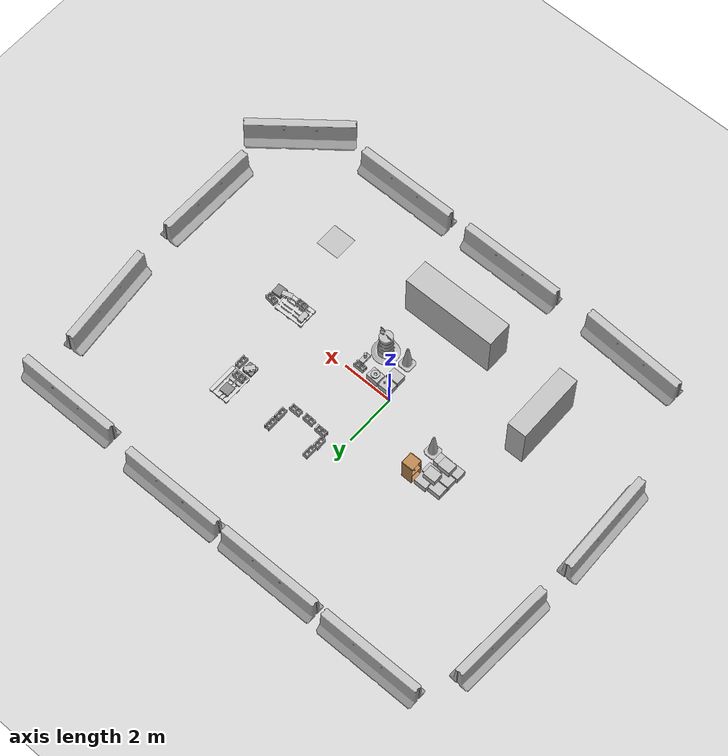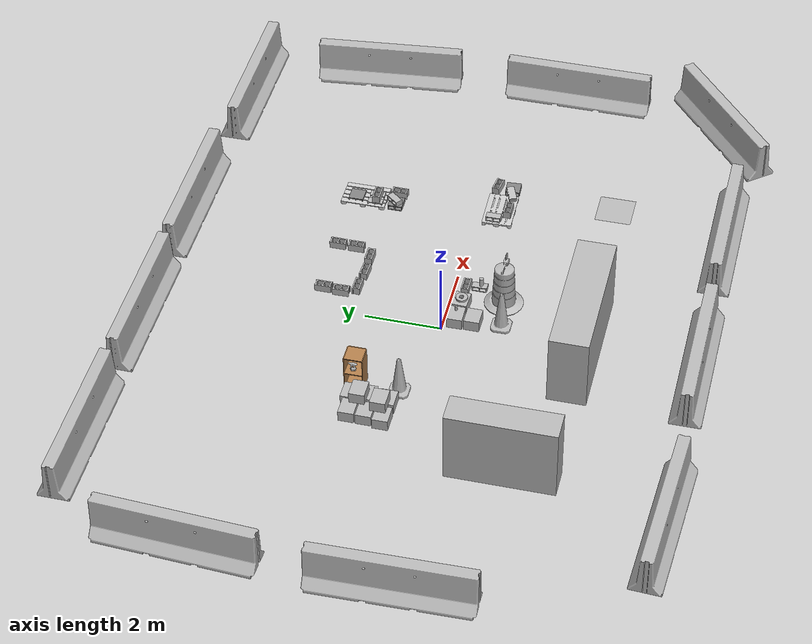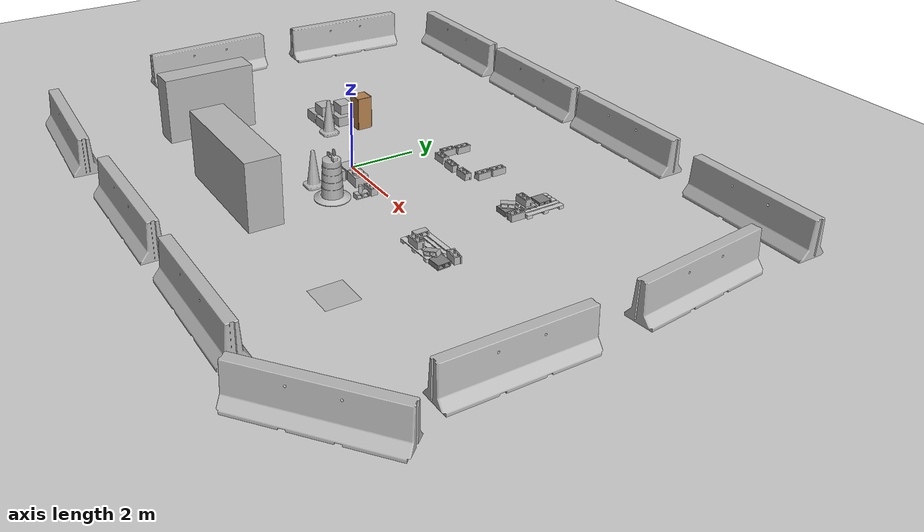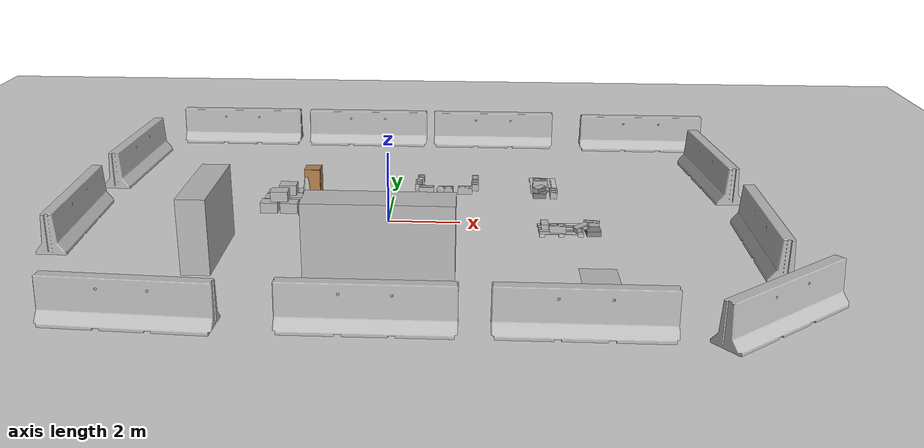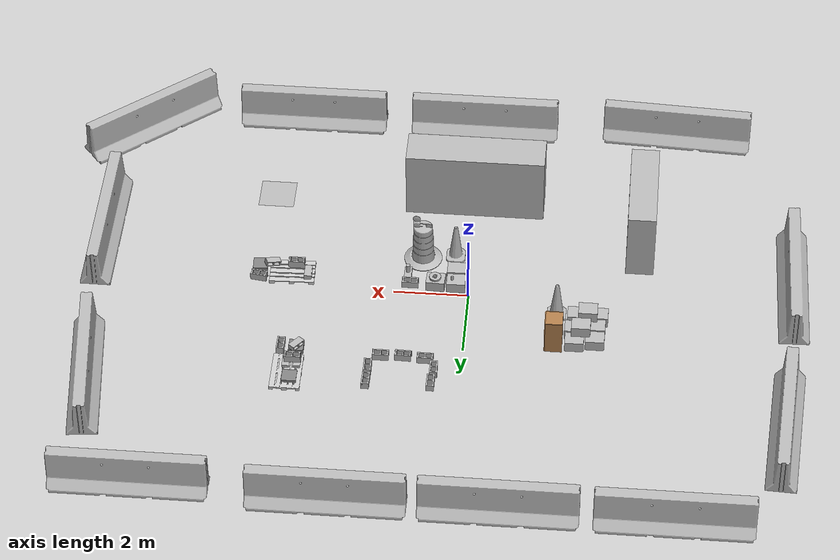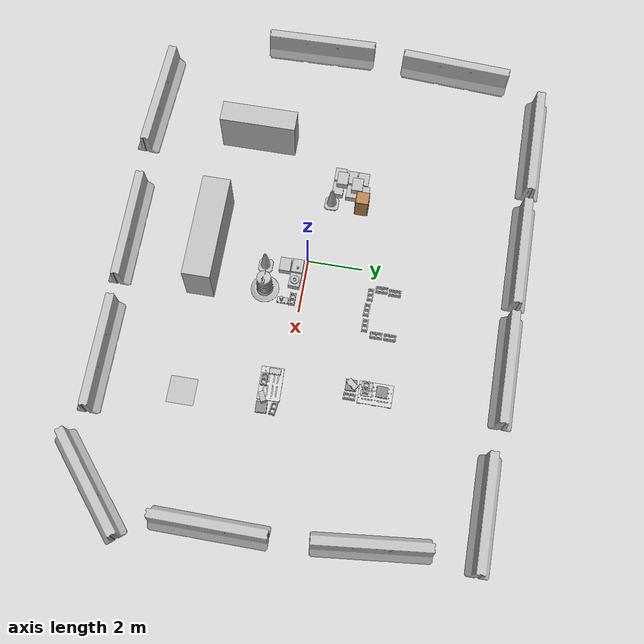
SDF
<sdf version="1.6">
 <world name="default">
  <light name="sun" type="directional">
   <pose>0 0 10 0 -0 0</pose>
   <diffuse>0.8 0.8 0.8 1</diffuse>
   <specular>0.2 0.2 0.2 1</specular>
   <attenuation>
    <range>1000</range>
    <constant>0.9</constant>
    <linear>0.01</linear>
    <quadratic>0.001</quadratic>
   </attenuation>
   <direction>-0.5 0.1 -0.9</direction>
  </light>
  <model name="ground_plane">
   <static>1</static>
   <link name="link">
    <collision name="collision">
     <geometry><plane><normal>0 0 1</normal><size>100 100</size></plane></geometry>
     <surface>
      <contact><collide_bitmask>65535</collide_bitmask></contact>
      <friction><ode><mu>100</mu><mu2>50</mu2></ode></friction>
     </surface>
    </collision>
    <visual name="visual">
     <cast_shadows>0</cast_shadows>
     <geometry><plane><normal>0 0 1</normal><size>100 100</size></plane></geometry>
     <material>
      <script><uri>file://media/materials/scripts/gazebo.material</uri><name>Gazebo/Grey</name></script>
     </material>
    </visual>
   </link>
  </model>
  <gravity>0 0 -9.8</gravity>
  <magnetic_field>6e-06 2.3e-05 -4.2e-05</magnetic_field>
  <atmosphere type="adiabatic"/>
  <physics name="default_physics" default="0" type="ode">
   <max_step_size>0.001</max_step_size>
   <real_time_factor>1</real_time_factor>
   <real_time_update_rate>1000</real_time_update_rate>
  </physics>
  <scene><ambient>0.4 0.4 0.4 1</ambient><background>0.7 0.7 0.7 1</background><shadows>1</shadows></scene>
  <audio><device>default</device></audio>
  <spherical_coordinates>
   <surface_model>EARTH_WGS84</surface_model>
   <latitude_deg>0</latitude_deg>
   <longitude_deg>0</longitude_deg>
   <elevation>0</elevation>
   <heading_deg>0</heading_deg>
  </spherical_coordinates>
  <model name="cinder_block">
   <link name="link">
    <inertial>
     <pose>0 0 0.1016 0 -0 0</pose>
     <mass>5</mass>
     <inertia>
      <ixx>0.028705</ixx>
      <ixy>0</ixy>
      <iyy>0.073708</iyy>
      <ixz>0</ixz>
      <iyz>0</iyz>
      <izz>0.06908</izz>
     </inertia>
    </inertial>
    <visual name="visual">
     <geometry><mesh><uri>model://cinder_block/meshes/cinder_block.dae</uri></mesh></geometry>
    </visual>
    <collision name="left">
     <pose>0 -0.08465 0.1016 0 -0 0</pose>
     <geometry><box><size>0.43495 0.0339 0.2032</size></box></geometry>
     <surface>
      <contact><ode><max_vel>0.1</max_vel><min_depth>0.001</min_depth></ode></contact>
      <friction><ode><mu>1</mu><mu2>1</mu2></ode></friction>
     </surface>
    </collision>
    <collision name="right">
     <pose>0 0.08465 0.1016 0 -0 0</pose>
     <geometry><box><size>0.43495 0.0339 0.2032</size></box></geometry>
     <surface>
      <contact><ode><max_vel>0.1</max_vel><min_depth>0.001</min_depth></ode></contact>
      <friction><ode><mu>1</mu><mu2>1</mu2></ode></friction>
     </surface>
    </collision>
    <collision name="front">
     <pose>0.18625 0 0.1016 0 -0 0</pose>
     <geometry><box><size>0.0339 0.1354 0.203</size></box></geometry>
     <surface>
      <contact><ode><max_vel>0.1</max_vel><min_depth>0.001</min_depth></ode></contact>
      <friction><ode><mu>1</mu><mu2>1</mu2></ode></friction>
     </surface>
    </collision>
    <collision name="middle">
     <pose>0 0 0.1016 0 -0 0</pose>
     <geometry><box><size>0.0339 0.1354 0.203</size></box></geometry>
     <surface>
      <contact><ode><max_vel>0.1</max_vel><min_depth>0.001</min_depth></ode></contact>
      <friction><ode><mu>1</mu><mu2>1</mu2></ode></friction>
     </surface>
    </collision>
    <collision name="back">
     <pose>-0.18625 0 0.1016 0 -0 0</pose>
     <geometry><box><size>0.0339 0.1354 0.203</size></box></geometry>
     <surface>
      <contact><ode><max_vel>0.1</max_vel><min_depth>0.001</min_depth></ode></contact>
      <friction><ode><mu>1</mu><mu2>1</mu2></ode></friction>
     </surface>
    </collision>
   </link>
   <pose>2.12256 2.41856 -1.2e-05 2.2e-05 2e-06 0</pose>
  </model>
  <model name="cinder_block_1">
   <link name="link">
    <inertial>
     <pose>0 0 0.1016 0 -0 0</pose>
     <mass>5</mass>
     <inertia>
      <ixx>0.028705</ixx>
      <ixy>0</ixy>
      <iyy>0.073708</iyy>
      <ixz>0</ixz>
      <iyz>0</iyz>
      <izz>0.06908</izz>
     </inertia>
    </inertial>
    <visual name="visual">
     <geometry><mesh><uri>model://cinder_block/meshes/cinder_block.dae</uri></mesh></geometry>
    </visual>
    <collision name="left">
     <pose>0 -0.08465 0.1016 0 -0 0</pose>
     <geometry><box><size>0.43495 0.0339 0.2032</size></box></geometry>
     <surface>
      <contact><ode><max_vel>0.1</max_vel><min_depth>0.001</min_depth></ode></contact>
      <friction><ode><mu>1</mu><mu2>1</mu2></ode></friction>
     </surface>
    </collision>
    <collision name="right">
     <pose>0 0.08465 0.1016 0 -0 0</pose>
     <geometry><box><size>0.43495 0.0339 0.2032</size></box></geometry>
     <surface>
      <contact><ode><max_vel>0.1</max_vel><min_depth>0.001</min_depth></ode></contact>
      <friction><ode><mu>1</mu><mu2>1</mu2></ode></friction>
     </surface>
    </collision>
    <collision name="front">
     <pose>0.18625 0 0.1016 0 -0 0</pose>
     <geometry><box><size>0.0339 0.1354 0.203</size></box></geometry>
     <surface>
      <contact><ode><max_vel>0.1</max_vel><min_depth>0.001</min_depth></ode></contact>
      <friction><ode><mu>1</mu><mu2>1</mu2></ode></friction>
     </surface>
    </collision>
    <collision name="middle">
     <pose>0 0 0.1016 0 -0 0</pose>
     <geometry><box><size>0.0339 0.1354 0.203</size></box></geometry>
     <surface>
      <contact><ode><max_vel>0.1</max_vel><min_depth>0.001</min_depth></ode></contact>
      <friction><ode><mu>1</mu><mu2>1</mu2></ode></friction>
     </surface>
    </collision>
    <collision name="back">
     <pose>-0.18625 0 0.1016 0 -0 0</pose>
     <geometry><box><size>0.0339 0.1354 0.203</size></box></geometry>
     <surface>
      <contact><ode><max_vel>0.1</max_vel><min_depth>0.001</min_depth></ode></contact>
      <friction><ode><mu>1</mu><mu2>1</mu2></ode></friction>
     </surface>
    </collision>
   </link>
   <pose>0.951418 2.44157 -0.000578 -8.1e-05 -3.7e-05 0</pose>
  </model>
  <model name="cinder_block_3">
   <link name="link">
    <inertial>
     <pose>0 0 0.1016 0 -0 0</pose>
     <mass>5</mass>
     <inertia>
      <ixx>0.028705</ixx>
      <ixy>0</ixy>
      <iyy>0.073708</iyy>
      <ixz>0</ixz>
      <iyz>0</iyz>
      <izz>0.06908</izz>
     </inertia>
    </inertial>
    <visual name="visual">
     <geometry><mesh><uri>model://cinder_block/meshes/cinder_block.dae</uri></mesh></geometry>
    </visual>
    <collision name="left">
     <pose>0 -0.08465 0.1016 0 -0 0</pose>
     <geometry><box><size>0.43495 0.0339 0.2032</size></box></geometry>
     <surface>
      <contact><ode><max_vel>0.1</max_vel><min_depth>0.001</min_depth></ode></contact>
      <friction><ode><mu>1</mu><mu2>1</mu2></ode></friction>
     </surface>
    </collision>
    <collision name="right">
     <pose>0 0.08465 0.1016 0 -0 0</pose>
     <geometry><box><size>0.43495 0.0339 0.2032</size></box></geometry>
     <surface>
      <contact><ode><max_vel>0.1</max_vel><min_depth>0.001</min_depth></ode></contact>
      <friction><ode><mu>1</mu><mu2>1</mu2></ode></friction>
     </surface>
    </collision>
    <collision name="front">
     <pose>0.18625 0 0.1016 0 -0 0</pose>
     <geometry><box><size>0.0339 0.1354 0.203</size></box></geometry>
     <surface>
      <contact><ode><max_vel>0.1</max_vel><min_depth>0.001</min_depth></ode></contact>
      <friction><ode><mu>1</mu><mu2>1</mu2></ode></friction>
     </surface>
    </collision>
    <collision name="middle">
     <pose>0 0 0.1016 0 -0 0</pose>
     <geometry><box><size>0.0339 0.1354 0.203</size></box></geometry>
     <surface>
      <contact><ode><max_vel>0.1</max_vel><min_depth>0.001</min_depth></ode></contact>
      <friction><ode><mu>1</mu><mu2>1</mu2></ode></friction>
     </surface>
    </collision>
    <collision name="back">
     <pose>-0.18625 0 0.1016 0 -0 0</pose>
     <geometry><box><size>0.0339 0.1354 0.203</size></box></geometry>
     <surface>
      <contact><ode><max_vel>0.1</max_vel><min_depth>0.001</min_depth></ode></contact>
      <friction><ode><mu>1</mu><mu2>1</mu2></ode></friction>
     </surface>
    </collision>
   </link>
   <pose>1.53729 2.39602 -6e-06 3.2e-05 -1.3e-05 3.10413</pose>
  </model>
  <model name="cinder_block_4">
   <link name="link">
    <inertial>
     <pose>0 0 0.1016 0 -0 0</pose>
     <mass>5</mass>
     <inertia>
      <ixx>0.028705</ixx>
      <ixy>0</ixy>
      <iyy>0.073708</iyy>
      <ixz>0</ixz>
      <iyz>0</iyz>
      <izz>0.06908</izz>
     </inertia>
    </inertial>
    <visual name="visual">
     <geometry><mesh><uri>model://cinder_block/meshes/cinder_block.dae</uri></mesh></geometry>
    </visual>
    <collision name="left">
     <pose>0 -0.08465 0.1016 0 -0 0</pose>
     <geometry><box><size>0.43495 0.0339 0.2032</size></box></geometry>
     <surface>
      <contact><ode><max_vel>0.1</max_vel><min_depth>0.001</min_depth></ode></contact>
      <friction><ode><mu>1</mu><mu2>1</mu2></ode></friction>
     </surface>
    </collision>
    <collision name="right">
     <pose>0 0.08465 0.1016 0 -0 0</pose>
     <geometry><box><size>0.43495 0.0339 0.2032</size></box></geometry>
     <surface>
      <contact><ode><max_vel>0.1</max_vel><min_depth>0.001</min_depth></ode></contact>
      <friction><ode><mu>1</mu><mu2>1</mu2></ode></friction>
     </surface>
    </collision>
    <collision name="front">
     <pose>0.18625 0 0.1016 0 -0 0</pose>
     <geometry><box><size>0.0339 0.1354 0.203</size></box></geometry>
     <surface>
      <contact><ode><max_vel>0.1</max_vel><min_depth>0.001</min_depth></ode></contact>
      <friction><ode><mu>1</mu><mu2>1</mu2></ode></friction>
     </surface>
    </collision>
    <collision name="middle">
     <pose>0 0 0.1016 0 -0 0</pose>
     <geometry><box><size>0.0339 0.1354 0.203</size></box></geometry>
     <surface>
      <contact><ode><max_vel>0.1</max_vel><min_depth>0.001</min_depth></ode></contact>
      <friction><ode><mu>1</mu><mu2>1</mu2></ode></friction>
     </surface>
    </collision>
    <collision name="back">
     <pose>-0.18625 0 0.1016 0 -0 0</pose>
     <geometry><box><size>0.0339 0.1354 0.203</size></box></geometry>
     <surface>
      <contact><ode><max_vel>0.1</max_vel><min_depth>0.001</min_depth></ode></contact>
      <friction><ode><mu>1</mu><mu2>1</mu2></ode></friction>
     </surface>
    </collision>
   </link>
   <pose>2.42783 2.86197 -6e-06 5.1e-05 4e-06 1.58286</pose>
  </model>
  <model name="cinder_block_6">
   <link name="link">
    <inertial>
     <pose>0 0 0.1016 0 -0 0</pose>
     <mass>5</mass>
     <inertia>
      <ixx>0.028705</ixx>
      <ixy>0</ixy>
      <iyy>0.073708</iyy>
      <ixz>0</ixz>
      <iyz>0</iyz>
      <izz>0.06908</izz>
     </inertia>
    </inertial>
    <visual name="visual">
     <geometry><mesh><uri>model://cinder_block/meshes/cinder_block.dae</uri></mesh></geometry>
    </visual>
    <collision name="left">
     <pose>0 -0.08465 0.1016 0 -0 0</pose>
     <geometry><box><size>0.43495 0.0339 0.2032</size></box></geometry>
     <surface>
      <contact><ode><max_vel>0.1</max_vel><min_depth>0.001</min_depth></ode></contact>
      <friction><ode><mu>1</mu><mu2>1</mu2></ode></friction>
     </surface>
    </collision>
    <collision name="right">
     <pose>0 0.08465 0.1016 0 -0 0</pose>
     <geometry><box><size>0.43495 0.0339 0.2032</size></box></geometry>
     <surface>
      <contact><ode><max_vel>0.1</max_vel><min_depth>0.001</min_depth></ode></contact>
      <friction><ode><mu>1</mu><mu2>1</mu2></ode></friction>
     </surface>
    </collision>
    <collision name="front">
     <pose>0.18625 0 0.1016 0 -0 0</pose>
     <geometry><box><size>0.0339 0.1354 0.203</size></box></geometry>
     <surface>
      <contact><ode><max_vel>0.1</max_vel><min_depth>0.001</min_depth></ode></contact>
      <friction><ode><mu>1</mu><mu2>1</mu2></ode></friction>
     </surface>
    </collision>
    <collision name="middle">
     <pose>0 0 0.1016 0 -0 0</pose>
     <geometry><box><size>0.0339 0.1354 0.203</size></box></geometry>
     <surface>
      <contact><ode><max_vel>0.1</max_vel><min_depth>0.001</min_depth></ode></contact>
      <friction><ode><mu>1</mu><mu2>1</mu2></ode></friction>
     </surface>
    </collision>
    <collision name="back">
     <pose>-0.18625 0 0.1016 0 -0 0</pose>
     <geometry><box><size>0.0339 0.1354 0.203</size></box></geometry>
     <surface>
      <contact><ode><max_vel>0.1</max_vel><min_depth>0.001</min_depth></ode></contact>
      <friction><ode><mu>1</mu><mu2>1</mu2></ode></friction>
     </surface>
    </collision>
   </link>
   <pose>2.43138 3.356 -6e-06 5.1e-05 4e-06 1.55629</pose>
  </model>
  <model name="cinder_block_7">
   <link name="link">
    <inertial>
     <pose>0 0 0.1016 0 -0 0</pose>
     <mass>5</mass>
     <inertia>
      <ixx>0.028705</ixx>
      <ixy>0</ixy>
      <iyy>0.073708</iyy>
      <ixz>0</ixz>
      <iyz>0</iyz>
      <izz>0.06908</izz>
     </inertia>
    </inertial>
    <visual name="visual">
     <geometry><mesh><uri>model://cinder_block/meshes/cinder_block.dae</uri></mesh></geometry>
    </visual>
    <collision name="left">
     <pose>0 -0.08465 0.1016 0 -0 0</pose>
     <geometry><box><size>0.43495 0.0339 0.2032</size></box></geometry>
     <surface>
      <contact><ode><max_vel>0.1</max_vel><min_depth>0.001</min_depth></ode></contact>
      <friction><ode><mu>1</mu><mu2>1</mu2></ode></friction>
     </surface>
    </collision>
    <collision name="right">
     <pose>0 0.08465 0.1016 0 -0 0</pose>
     <geometry><box><size>0.43495 0.0339 0.2032</size></box></geometry>
     <surface>
      <contact><ode><max_vel>0.1</max_vel><min_depth>0.001</min_depth></ode></contact>
      <friction><ode><mu>1</mu><mu2>1</mu2></ode></friction>
     </surface>
    </collision>
    <collision name="front">
     <pose>0.18625 0 0.1016 0 -0 0</pose>
     <geometry><box><size>0.0339 0.1354 0.203</size></box></geometry>
     <surface>
      <contact><ode><max_vel>0.1</max_vel><min_depth>0.001</min_depth></ode></contact>
      <friction><ode><mu>1</mu><mu2>1</mu2></ode></friction>
     </surface>
    </collision>
    <collision name="middle">
     <pose>0 0 0.1016 0 -0 0</pose>
     <geometry><box><size>0.0339 0.1354 0.203</size></box></geometry>
     <surface>
      <contact><ode><max_vel>0.1</max_vel><min_depth>0.001</min_depth></ode></contact>
      <friction><ode><mu>1</mu><mu2>1</mu2></ode></friction>
     </surface>
    </collision>
    <collision name="back">
     <pose>-0.18625 0 0.1016 0 -0 0</pose>
     <geometry><box><size>0.0339 0.1354 0.203</size></box></geometry>
     <surface>
      <contact><ode><max_vel>0.1</max_vel><min_depth>0.001</min_depth></ode></contact>
      <friction><ode><mu>1</mu><mu2>1</mu2></ode></friction>
     </surface>
    </collision>
   </link>
   <pose>0.703882 2.81906 -6e-06 5.1e-05 4e-06 1.58968</pose>
  </model>
  <model name="cinder_block_9">
   <link name="link">
    <inertial>
     <pose>0 0 0.1016 0 -0 0</pose>
     <mass>5</mass>
     <inertia>
      <ixx>0.028705</ixx>
      <ixy>0</ixy>
      <iyy>0.073708</iyy>
      <ixz>0</ixz>
      <iyz>0</iyz>
      <izz>0.06908</izz>
     </inertia>
    </inertial>
    <visual name="visual">
     <geometry><mesh><uri>model://cinder_block/meshes/cinder_block.dae</uri></mesh></geometry>
    </visual>
    <collision name="left">
     <pose>0 -0.08465 0.1016 0 -0 0</pose>
     <geometry><box><size>0.43495 0.0339 0.2032</size></box></geometry>
     <surface>
      <contact><ode><max_vel>0.1</max_vel><min_depth>0.001</min_depth></ode></contact>
      <friction><ode><mu>1</mu><mu2>1</mu2></ode></friction>
     </surface>
    </collision>
    <collision name="right">
     <pose>0 0.08465 0.1016 0 -0 0</pose>
     <geometry><box><size>0.43495 0.0339 0.2032</size></box></geometry>
     <surface>
      <contact><ode><max_vel>0.1</max_vel><min_depth>0.001</min_depth></ode></contact>
      <friction><ode><mu>1</mu><mu2>1</mu2></ode></friction>
     </surface>
    </collision>
    <collision name="front">
     <pose>0.18625 0 0.1016 0 -0 0</pose>
     <geometry><box><size>0.0339 0.1354 0.203</size></box></geometry>
     <surface>
      <contact><ode><max_vel>0.1</max_vel><min_depth>0.001</min_depth></ode></contact>
      <friction><ode><mu>1</mu><mu2>1</mu2></ode></friction>
     </surface>
    </collision>
    <collision name="middle">
     <pose>0 0 0.1016 0 -0 0</pose>
     <geometry><box><size>0.0339 0.1354 0.203</size></box></geometry>
     <surface>
      <contact><ode><max_vel>0.1</max_vel><min_depth>0.001</min_depth></ode></contact>
      <friction><ode><mu>1</mu><mu2>1</mu2></ode></friction>
     </surface>
    </collision>
    <collision name="back">
     <pose>-0.18625 0 0.1016 0 -0 0</pose>
     <geometry><box><size>0.0339 0.1354 0.203</size></box></geometry>
     <surface>
      <contact><ode><max_vel>0.1</max_vel><min_depth>0.001</min_depth></ode></contact>
      <friction><ode><mu>1</mu><mu2>1</mu2></ode></friction>
     </surface>
    </collision>
   </link>
   <pose>0.746762 3.29994 -1.2e-05 5.8e-05 5e-06 1.57094</pose>
  </model>
  <model name="brick_box_3x1x3">
   <static>1</static>
   <link name="chassis">
    <pose>0 0 1.5 0 -0 0</pose>
    <collision name="collision"><geometry><box><size>2.75 0.75 2</size></box></geometry></collision>
    <visual name="visual">
     <geometry>
      <mesh><uri>model://brick_box_3x1x3/meshes/simple_box.dae</uri><scale>2.75 0.75 2</scale></mesh>
     </geometry>
     <material>
      <script>
       <uri>model://brick_box_3x1x3/materials/scripts</uri>
       <uri>model://brick_box_3x1x3/materials/textures</uri>
       <name>BrickBox/Diffuse</name>
      </script>
     </material>
    </visual>
   </link>
   <pose>-4.50649 -2.57251 -0.500406 0 -0 1.57353</pose>
  </model>
  <model name="brick_box_3x1x3_0">
   <static>1</static>
   <link name="chassis">
    <pose>0 0 1.5 0 -0 0</pose>
    <collision name="collision"><geometry><box><size>3.75 1 2</size></box></geometry></collision>
    <visual name="visual">
     <geometry>
      <mesh><uri>model://brick_box_3x1x3/meshes/simple_box.dae</uri><scale>3.75 1 2</scale></mesh>
     </geometry>
     <material>
      <script>
       <uri>model://brick_box_3x1x3/materials/scripts</uri>
       <uri>model://brick_box_3x1x3/materials/textures</uri>
       <name>BrickBox/Diffuse</name>
      </script>
     </material>
    </visual>
   </link>
   <pose>0.059682 -3.58681 -0.4981 0 -0 0</pose>
  </model>
  <model name="euro_pallet_static">
   <link name="link">
    <inertial>
     <mass>20</mass>
     <inertia><ixx>2.43</ixx><ixy>0</ixy><ixz>0</ixz><iyy>1.1</iyy><iyz>0</iyz><izz>3.47</izz></inertia>
    </inertial>
    <visual name="visual">
     <pose>0 0 0.05 0 -0 0</pose>
     <geometry><mesh><uri>model://euro_pallet/meshes/pallet.dae</uri><scale>0.1 0.1 0.1</scale></mesh></geometry>
    </visual>
    <collision name="collision">
     <pose>0 0 0.05 0 -0 0</pose>
     <geometry>
      <mesh><uri>~/.gazebo/models/euro_pallet/meshes/pallet.dae</uri><scale>0.1 0.1 0.1</scale></mesh>
     </geometry>
     <surface>
      <friction>
       <ode><mu>1</mu><mu2>1</mu2><fdir1>0 0 0</fdir1><slip1>0</slip1><slip2>0</slip2></ode>
       <torsional>
        <coefficient>1</coefficient>
        <patch_radius>0</patch_radius>
        <surface_radius>0</surface_radius>
        <use_patch_radius>1</use_patch_radius>
        <ode><slip>0</slip></ode>
       </torsional>
      </friction>
      <bounce><restitution_coefficient>0</restitution_coefficient><threshold>1e+06</threshold></bounce>
      <contact>
       <collide_without_contact>0</collide_without_contact>
       <collide_without_contact_bitmask>1</collide_without_contact_bitmask>
       <collide_bitmask>1</collide_bitmask>
       <ode>
        <soft_cfm>0</soft_cfm>
        <soft_erp>0.2</soft_erp>
        <kp>1e+13</kp>
        <kd>1</kd>
        <max_vel>0.01</max_vel>
        <min_depth>0</min_depth>
       </ode>
       <bullet>
        <split_impulse>1</split_impulse>
        <split_impulse_penetration_threshold>-0.01</split_impulse_penetration_threshold>
        <soft_cfm>0</soft_cfm>
        <soft_erp>0.2</soft_erp>
        <kp>1e+13</kp>
        <kd>1</kd>
       </bullet>
      </contact>
     </surface>
    </collision>
   </link>
   <static>1</static>
   <pose>4.52441 3.15783 0 0 -0 0</pose>
  </model>
  <model name="cinder_block_2_static">
   <link name="link">
    <inertial>
     <pose>0 0 0.071438 0 -0 0</pose>
     <mass>5</mass>
     <inertia>
      <ixx>0.06908</ixx>
      <ixy>0</ixy>
      <iyy>0.028705</iyy>
      <ixz>0</ixz>
      <iyz>0</iyz>
      <izz>0.073708</izz>
     </inertia>
    </inertial>
    <visual name="visual">
     <geometry><mesh><uri>model://cinder_block_2/meshes/cinder_block.dae</uri></mesh></geometry>
    </visual>
    <collision name="top">
     <pose>0 0 0.130175 0 -0 0</pose>
     <geometry><box><size>0.19368 0.396875 0.0254</size></box></geometry>
     <surface>
      <friction>
       <ode><mu>1</mu><mu2>1</mu2><fdir1>0 0 0</fdir1><slip1>0</slip1><slip2>0</slip2></ode>
       <torsional>
        <coefficient>1</coefficient>
        <patch_radius>0</patch_radius>
        <surface_radius>0</surface_radius>
        <use_patch_radius>1</use_patch_radius>
        <ode><slip>0</slip></ode>
       </torsional>
      </friction>
      <bounce><restitution_coefficient>0</restitution_coefficient><threshold>1e+06</threshold></bounce>
      <contact>
       <collide_without_contact>0</collide_without_contact>
       <collide_without_contact_bitmask>1</collide_without_contact_bitmask>
       <collide_bitmask>1</collide_bitmask>
       <ode>
        <soft_cfm>0</soft_cfm>
        <soft_erp>0.2</soft_erp>
        <kp>1e+13</kp>
        <kd>1</kd>
        <max_vel>0.1</max_vel>
        <min_depth>0.001</min_depth>
       </ode>
       <bullet>
        <split_impulse>1</split_impulse>
        <split_impulse_penetration_threshold>-0.01</split_impulse_penetration_threshold>
        <soft_cfm>0</soft_cfm>
        <soft_erp>0.2</soft_erp>
        <kp>1e+13</kp>
        <kd>1</kd>
       </bullet>
      </contact>
     </surface>
    </collision>
    <collision name="bottom">
     <pose>0 0 0.0127 0 -0 0</pose>
     <geometry><box><size>0.19368 0.396875 0.0254</size></box></geometry>
     <surface>
      <friction>
       <ode><mu>1</mu><mu2>1</mu2><fdir1>0 0 0</fdir1><slip1>0</slip1><slip2>0</slip2></ode>
       <torsional>
        <coefficient>1</coefficient>
        <patch_radius>0</patch_radius>
        <surface_radius>0</surface_radius>
        <use_patch_radius>1</use_patch_radius>
        <ode><slip>0</slip></ode>
       </torsional>
      </friction>
      <bounce><restitution_coefficient>0</restitution_coefficient><threshold>1e+06</threshold></bounce>
      <contact>
       <collide_without_contact>0</collide_without_contact>
       <collide_without_contact_bitmask>1</collide_without_contact_bitmask>
       <collide_bitmask>1</collide_bitmask>
       <ode>
        <soft_cfm>0</soft_cfm>
        <soft_erp>0.2</soft_erp>
        <kp>1e+13</kp>
        <kd>1</kd>
        <max_vel>0.1</max_vel>
        <min_depth>0.001</min_depth>
       </ode>
       <bullet>
        <split_impulse>1</split_impulse>
        <split_impulse_penetration_threshold>-0.01</split_impulse_penetration_threshold>
        <soft_cfm>0</soft_cfm>
        <soft_erp>0.2</soft_erp>
        <kp>1e+13</kp>
        <kd>1</kd>
       </bullet>
      </contact>
     </surface>
    </collision>
    <collision name="left">
     <pose>0 -0.185738 0.071438 0 -0 0</pose>
     <geometry><box><size>0.19368 0.0254 0.092075</size></box></geometry>
     <surface>
      <friction>
       <ode><mu>1</mu><mu2>1</mu2><fdir1>0 0 0</fdir1><slip1>0</slip1><slip2>0</slip2></ode>
       <torsional>
        <coefficient>1</coefficient>
        <patch_radius>0</patch_radius>
        <surface_radius>0</surface_radius>
        <use_patch_radius>1</use_patch_radius>
        <ode><slip>0</slip></ode>
       </torsional>
      </friction>
      <bounce><restitution_coefficient>0</restitution_coefficient><threshold>1e+06</threshold></bounce>
      <contact>
       <collide_without_contact>0</collide_without_contact>
       <collide_without_contact_bitmask>1</collide_without_contact_bitmask>
       <collide_bitmask>1</collide_bitmask>
       <ode>
        <soft_cfm>0</soft_cfm>
        <soft_erp>0.2</soft_erp>
        <kp>1e+13</kp>
        <kd>1</kd>
        <max_vel>0.1</max_vel>
        <min_depth>0.001</min_depth>
       </ode>
       <bullet>
        <split_impulse>1</split_impulse>
        <split_impulse_penetration_threshold>-0.01</split_impulse_penetration_threshold>
        <soft_cfm>0</soft_cfm>
        <soft_erp>0.2</soft_erp>
        <kp>1e+13</kp>
        <kd>1</kd>
       </bullet>
      </contact>
     </surface>
    </collision>
    <collision name="middle">
     <pose>0 0 0.071438 0 -0 0</pose>
     <geometry><box><size>0.19368 0.0254 0.092075</size></box></geometry>
     <surface>
      <friction>
       <ode><mu>1</mu><mu2>1</mu2><fdir1>0 0 0</fdir1><slip1>0</slip1><slip2>0</slip2></ode>
       <torsional>
        <coefficient>1</coefficient>
        <patch_radius>0</patch_radius>
        <surface_radius>0</surface_radius>
        <use_patch_radius>1</use_patch_radius>
        <ode><slip>0</slip></ode>
       </torsional>
      </friction>
      <bounce><restitution_coefficient>0</restitution_coefficient><threshold>1e+06</threshold></bounce>
      <contact>
       <collide_without_contact>0</collide_without_contact>
       <collide_without_contact_bitmask>1</collide_without_contact_bitmask>
       <collide_bitmask>1</collide_bitmask>
       <ode>
        <soft_cfm>0</soft_cfm>
        <soft_erp>0.2</soft_erp>
        <kp>1e+13</kp>
        <kd>1</kd>
        <max_vel>0.1</max_vel>
        <min_depth>0.001</min_depth>
       </ode>
       <bullet>
        <split_impulse>1</split_impulse>
        <split_impulse_penetration_threshold>-0.01</split_impulse_penetration_threshold>
        <soft_cfm>0</soft_cfm>
        <soft_erp>0.2</soft_erp>
        <kp>1e+13</kp>
        <kd>1</kd>
       </bullet>
      </contact>
     </surface>
    </collision>
    <collision name="right">
     <pose>0 0.185738 0.071438 0 -0 0</pose>
     <geometry><box><size>0.19368 0.0254 0.092075</size></box></geometry>
     <surface>
      <friction>
       <ode><mu>1</mu><mu2>1</mu2><fdir1>0 0 0</fdir1><slip1>0</slip1><slip2>0</slip2></ode>
       <torsional>
        <coefficient>1</coefficient>
        <patch_radius>0</patch_radius>
        <surface_radius>0</surface_radius>
        <use_patch_radius>1</use_patch_radius>
        <ode><slip>0</slip></ode>
       </torsional>
      </friction>
      <bounce><restitution_coefficient>0</restitution_coefficient><threshold>1e+06</threshold></bounce>
      <contact>
       <collide_without_contact>0</collide_without_contact>
       <collide_without_contact_bitmask>1</collide_without_contact_bitmask>
       <collide_bitmask>1</collide_bitmask>
       <ode>
        <soft_cfm>0</soft_cfm>
        <soft_erp>0.2</soft_erp>
        <kp>1e+13</kp>
        <kd>1</kd>
        <max_vel>0.1</max_vel>
        <min_depth>0.001</min_depth>
       </ode>
       <bullet>
        <split_impulse>1</split_impulse>
        <split_impulse_penetration_threshold>-0.01</split_impulse_penetration_threshold>
        <soft_cfm>0</soft_cfm>
        <soft_erp>0.2</soft_erp>
        <kp>1e+13</kp>
        <kd>1</kd>
       </bullet>
      </contact>
     </surface>
    </collision>
   </link>
   <static>1</static>
   <pose>4.27578 2.8283 0 0 -0 0</pose>
  </model>
  <model name="cinder_block_2_static_0">
   <link name="link">
    <inertial>
     <pose>0 0 0.071438 0 -0 0</pose>
     <mass>5</mass>
     <inertia>
      <ixx>0.06908</ixx>
      <ixy>0</ixy>
      <iyy>0.028705</iyy>
      <ixz>0</ixz>
      <iyz>0</iyz>
      <izz>0.073708</izz>
     </inertia>
    </inertial>
    <visual name="visual">
     <geometry><mesh><uri>model://cinder_block_2/meshes/cinder_block.dae</uri></mesh></geometry>
    </visual>
    <collision name="top">
     <pose>0 0 0.130175 0 -0 0</pose>
     <geometry><box><size>0.19368 0.396875 0.0254</size></box></geometry>
     <surface>
      <friction>
       <ode><mu>1</mu><mu2>1</mu2><fdir1>0 0 0</fdir1><slip1>0</slip1><slip2>0</slip2></ode>
       <torsional>
        <coefficient>1</coefficient>
        <patch_radius>0</patch_radius>
        <surface_radius>0</surface_radius>
        <use_patch_radius>1</use_patch_radius>
        <ode><slip>0</slip></ode>
       </torsional>
      </friction>
      <bounce><restitution_coefficient>0</restitution_coefficient><threshold>1e+06</threshold></bounce>
      <contact>
       <collide_without_contact>0</collide_without_contact>
       <collide_without_contact_bitmask>1</collide_without_contact_bitmask>
       <collide_bitmask>1</collide_bitmask>
       <ode>
        <soft_cfm>0</soft_cfm>
        <soft_erp>0.2</soft_erp>
        <kp>1e+13</kp>
        <kd>1</kd>
        <max_vel>0.1</max_vel>
        <min_depth>0.001</min_depth>
       </ode>
       <bullet>
        <split_impulse>1</split_impulse>
        <split_impulse_penetration_threshold>-0.01</split_impulse_penetration_threshold>
        <soft_cfm>0</soft_cfm>
        <soft_erp>0.2</soft_erp>
        <kp>1e+13</kp>
        <kd>1</kd>
       </bullet>
      </contact>
     </surface>
    </collision>
    <collision name="bottom">
     <pose>0 0 0.0127 0 -0 0</pose>
     <geometry><box><size>0.19368 0.396875 0.0254</size></box></geometry>
     <surface>
      <friction>
       <ode><mu>1</mu><mu2>1</mu2><fdir1>0 0 0</fdir1><slip1>0</slip1><slip2>0</slip2></ode>
       <torsional>
        <coefficient>1</coefficient>
        <patch_radius>0</patch_radius>
        <surface_radius>0</surface_radius>
        <use_patch_radius>1</use_patch_radius>
        <ode><slip>0</slip></ode>
       </torsional>
      </friction>
      <bounce><restitution_coefficient>0</restitution_coefficient><threshold>1e+06</threshold></bounce>
      <contact>
       <collide_without_contact>0</collide_without_contact>
       <collide_without_contact_bitmask>1</collide_without_contact_bitmask>
       <collide_bitmask>1</collide_bitmask>
       <ode>
        <soft_cfm>0</soft_cfm>
        <soft_erp>0.2</soft_erp>
        <kp>1e+13</kp>
        <kd>1</kd>
        <max_vel>0.1</max_vel>
        <min_depth>0.001</min_depth>
       </ode>
       <bullet>
        <split_impulse>1</split_impulse>
        <split_impulse_penetration_threshold>-0.01</split_impulse_penetration_threshold>
        <soft_cfm>0</soft_cfm>
        <soft_erp>0.2</soft_erp>
        <kp>1e+13</kp>
        <kd>1</kd>
       </bullet>
      </contact>
     </surface>
    </collision>
    <collision name="left">
     <pose>0 -0.185738 0.071438 0 -0 0</pose>
     <geometry><box><size>0.19368 0.0254 0.092075</size></box></geometry>
     <surface>
      <friction>
       <ode><mu>1</mu><mu2>1</mu2><fdir1>0 0 0</fdir1><slip1>0</slip1><slip2>0</slip2></ode>
       <torsional>
        <coefficient>1</coefficient>
        <patch_radius>0</patch_radius>
        <surface_radius>0</surface_radius>
        <use_patch_radius>1</use_patch_radius>
        <ode><slip>0</slip></ode>
       </torsional>
      </friction>
      <bounce><restitution_coefficient>0</restitution_coefficient><threshold>1e+06</threshold></bounce>
      <contact>
       <collide_without_contact>0</collide_without_contact>
       <collide_without_contact_bitmask>1</collide_without_contact_bitmask>
       <collide_bitmask>1</collide_bitmask>
       <ode>
        <soft_cfm>0</soft_cfm>
        <soft_erp>0.2</soft_erp>
        <kp>1e+13</kp>
        <kd>1</kd>
        <max_vel>0.1</max_vel>
        <min_depth>0.001</min_depth>
       </ode>
       <bullet>
        <split_impulse>1</split_impulse>
        <split_impulse_penetration_threshold>-0.01</split_impulse_penetration_threshold>
        <soft_cfm>0</soft_cfm>
        <soft_erp>0.2</soft_erp>
        <kp>1e+13</kp>
        <kd>1</kd>
       </bullet>
      </contact>
     </surface>
    </collision>
    <collision name="middle">
     <pose>0 0 0.071438 0 -0 0</pose>
     <geometry><box><size>0.19368 0.0254 0.092075</size></box></geometry>
     <surface>
      <friction>
       <ode><mu>1</mu><mu2>1</mu2><fdir1>0 0 0</fdir1><slip1>0</slip1><slip2>0</slip2></ode>
       <torsional>
        <coefficient>1</coefficient>
        <patch_radius>0</patch_radius>
        <surface_radius>0</surface_radius>
        <use_patch_radius>1</use_patch_radius>
        <ode><slip>0</slip></ode>
       </torsional>
      </friction>
      <bounce><restitution_coefficient>0</restitution_coefficient><threshold>1e+06</threshold></bounce>
      <contact>
       <collide_without_contact>0</collide_without_contact>
       <collide_without_contact_bitmask>1</collide_without_contact_bitmask>
       <collide_bitmask>1</collide_bitmask>
       <ode>
        <soft_cfm>0</soft_cfm>
        <soft_erp>0.2</soft_erp>
        <kp>1e+13</kp>
        <kd>1</kd>
        <max_vel>0.1</max_vel>
        <min_depth>0.001</min_depth>
       </ode>
       <bullet>
        <split_impulse>1</split_impulse>
        <split_impulse_penetration_threshold>-0.01</split_impulse_penetration_threshold>
        <soft_cfm>0</soft_cfm>
        <soft_erp>0.2</soft_erp>
        <kp>1e+13</kp>
        <kd>1</kd>
       </bullet>
      </contact>
     </surface>
    </collision>
    <collision name="right">
     <pose>0 0.185738 0.071438 0 -0 0</pose>
     <geometry><box><size>0.19368 0.0254 0.092075</size></box></geometry>
     <surface>
      <friction>
       <ode><mu>1</mu><mu2>1</mu2><fdir1>0 0 0</fdir1><slip1>0</slip1><slip2>0</slip2></ode>
       <torsional>
        <coefficient>1</coefficient>
        <patch_radius>0</patch_radius>
        <surface_radius>0</surface_radius>
        <use_patch_radius>1</use_patch_radius>
        <ode><slip>0</slip></ode>
       </torsional>
      </friction>
      <bounce><restitution_coefficient>0</restitution_coefficient><threshold>1e+06</threshold></bounce>
      <contact>
       <collide_without_contact>0</collide_without_contact>
       <collide_without_contact_bitmask>1</collide_without_contact_bitmask>
       <collide_bitmask>1</collide_bitmask>
       <ode>
        <soft_cfm>0</soft_cfm>
        <soft_erp>0.2</soft_erp>
        <kp>1e+13</kp>
        <kd>1</kd>
        <max_vel>0.1</max_vel>
        <min_depth>0.001</min_depth>
       </ode>
       <bullet>
        <split_impulse>1</split_impulse>
        <split_impulse_penetration_threshold>-0.01</split_impulse_penetration_threshold>
        <soft_cfm>0</soft_cfm>
        <soft_erp>0.2</soft_erp>
        <kp>1e+13</kp>
        <kd>1</kd>
       </bullet>
      </contact>
     </surface>
    </collision>
   </link>
   <static>1</static>
   <pose>4.56736 2.83532 0 0 -0 0</pose>
  </model>
  <model name="cinder_block_static">
   <link name="link">
    <inertial>
     <pose>0 0 0.1016 0 -0 0</pose>
     <mass>5</mass>
     <inertia>
      <ixx>0.028705</ixx>
      <ixy>0</ixy>
      <iyy>0.073708</iyy>
      <ixz>0</ixz>
      <iyz>0</iyz>
      <izz>0.06908</izz>
     </inertia>
    </inertial>
    <visual name="visual">
     <geometry><mesh><uri>model://cinder_block/meshes/cinder_block.dae</uri></mesh></geometry>
    </visual>
    <collision name="left">
     <pose>0 -0.08465 0.1016 0 -0 0</pose>
     <geometry><box><size>0.43495 0.0339 0.2032</size></box></geometry>
     <surface>
      <friction>
       <ode><mu>1</mu><mu2>1</mu2><fdir1>0 0 0</fdir1><slip1>0</slip1><slip2>0</slip2></ode>
       <torsional>
        <coefficient>1</coefficient>
        <patch_radius>0</patch_radius>
        <surface_radius>0</surface_radius>
        <use_patch_radius>1</use_patch_radius>
        <ode><slip>0</slip></ode>
       </torsional>
      </friction>
      <bounce><restitution_coefficient>0</restitution_coefficient><threshold>1e+06</threshold></bounce>
      <contact>
       <collide_without_contact>0</collide_without_contact>
       <collide_without_contact_bitmask>1</collide_without_contact_bitmask>
       <collide_bitmask>1</collide_bitmask>
       <ode>
        <soft_cfm>0</soft_cfm>
        <soft_erp>0.2</soft_erp>
        <kp>1e+13</kp>
        <kd>1</kd>
        <max_vel>0.1</max_vel>
        <min_depth>0.001</min_depth>
       </ode>
       <bullet>
        <split_impulse>1</split_impulse>
        <split_impulse_penetration_threshold>-0.01</split_impulse_penetration_threshold>
        <soft_cfm>0</soft_cfm>
        <soft_erp>0.2</soft_erp>
        <kp>1e+13</kp>
        <kd>1</kd>
       </bullet>
      </contact>
     </surface>
    </collision>
    <collision name="right">
     <pose>0 0.08465 0.1016 0 -0 0</pose>
     <geometry><box><size>0.43495 0.0339 0.2032</size></box></geometry>
     <surface>
      <friction>
       <ode><mu>1</mu><mu2>1</mu2><fdir1>0 0 0</fdir1><slip1>0</slip1><slip2>0</slip2></ode>
       <torsional>
        <coefficient>1</coefficient>
        <patch_radius>0</patch_radius>
        <surface_radius>0</surface_radius>
        <use_patch_radius>1</use_patch_radius>
        <ode><slip>0</slip></ode>
       </torsional>
      </friction>
      <bounce><restitution_coefficient>0</restitution_coefficient><threshold>1e+06</threshold></bounce>
      <contact>
       <collide_without_contact>0</collide_without_contact>
       <collide_without_contact_bitmask>1</collide_without_contact_bitmask>
       <collide_bitmask>1</collide_bitmask>
       <ode>
        <soft_cfm>0</soft_cfm>
        <soft_erp>0.2</soft_erp>
        <kp>1e+13</kp>
        <kd>1</kd>
        <max_vel>0.1</max_vel>
        <min_depth>0.001</min_depth>
       </ode>
       <bullet>
        <split_impulse>1</split_impulse>
        <split_impulse_penetration_threshold>-0.01</split_impulse_penetration_threshold>
        <soft_cfm>0</soft_cfm>
        <soft_erp>0.2</soft_erp>
        <kp>1e+13</kp>
        <kd>1</kd>
       </bullet>
      </contact>
     </surface>
    </collision>
    <collision name="front">
     <pose>0.18625 0 0.1016 0 -0 0</pose>
     <geometry><box><size>0.0339 0.1354 0.203</size></box></geometry>
     <surface>
      <friction>
       <ode><mu>1</mu><mu2>1</mu2><fdir1>0 0 0</fdir1><slip1>0</slip1><slip2>0</slip2></ode>
       <torsional>
        <coefficient>1</coefficient>
        <patch_radius>0</patch_radius>
        <surface_radius>0</surface_radius>
        <use_patch_radius>1</use_patch_radius>
        <ode><slip>0</slip></ode>
       </torsional>
      </friction>
      <bounce><restitution_coefficient>0</restitution_coefficient><threshold>1e+06</threshold></bounce>
      <contact>
       <collide_without_contact>0</collide_without_contact>
       <collide_without_contact_bitmask>1</collide_without_contact_bitmask>
       <collide_bitmask>1</collide_bitmask>
       <ode>
        <soft_cfm>0</soft_cfm>
        <soft_erp>0.2</soft_erp>
        <kp>1e+13</kp>
        <kd>1</kd>
        <max_vel>0.1</max_vel>
        <min_depth>0.001</min_depth>
       </ode>
       <bullet>
        <split_impulse>1</split_impulse>
        <split_impulse_penetration_threshold>-0.01</split_impulse_penetration_threshold>
        <soft_cfm>0</soft_cfm>
        <soft_erp>0.2</soft_erp>
        <kp>1e+13</kp>
        <kd>1</kd>
       </bullet>
      </contact>
     </surface>
    </collision>
    <collision name="middle">
     <pose>0 0 0.1016 0 -0 0</pose>
     <geometry><box><size>0.0339 0.1354 0.203</size></box></geometry>
     <surface>
      <friction>
       <ode><mu>1</mu><mu2>1</mu2><fdir1>0 0 0</fdir1><slip1>0</slip1><slip2>0</slip2></ode>
       <torsional>
        <coefficient>1</coefficient>
        <patch_radius>0</patch_radius>
        <surface_radius>0</surface_radius>
        <use_patch_radius>1</use_patch_radius>
        <ode><slip>0</slip></ode>
       </torsional>
      </friction>
      <bounce><restitution_coefficient>0</restitution_coefficient><threshold>1e+06</threshold></bounce>
      <contact>
       <collide_without_contact>0</collide_without_contact>
       <collide_without_contact_bitmask>1</collide_without_contact_bitmask>
       <collide_bitmask>1</collide_bitmask>
       <ode>
        <soft_cfm>0</soft_cfm>
        <soft_erp>0.2</soft_erp>
        <kp>1e+13</kp>
        <kd>1</kd>
        <max_vel>0.1</max_vel>
        <min_depth>0.001</min_depth>
       </ode>
       <bullet>
        <split_impulse>1</split_impulse>
        <split_impulse_penetration_threshold>-0.01</split_impulse_penetration_threshold>
        <soft_cfm>0</soft_cfm>
        <soft_erp>0.2</soft_erp>
        <kp>1e+13</kp>
        <kd>1</kd>
       </bullet>
      </contact>
     </surface>
    </collision>
    <collision name="back">
     <pose>-0.18625 0 0.1016 0 -0 0</pose>
     <geometry><box><size>0.0339 0.1354 0.203</size></box></geometry>
     <surface>
      <friction>
       <ode><mu>1</mu><mu2>1</mu2><fdir1>0 0 0</fdir1><slip1>0</slip1><slip2>0</slip2></ode>
       <torsional>
        <coefficient>1</coefficient>
        <patch_radius>0</patch_radius>
        <surface_radius>0</surface_radius>
        <use_patch_radius>1</use_patch_radius>
        <ode><slip>0</slip></ode>
       </torsional>
      </friction>
      <bounce><restitution_coefficient>0</restitution_coefficient><threshold>1e+06</threshold></bounce>
      <contact>
       <collide_without_contact>0</collide_without_contact>
       <collide_without_contact_bitmask>1</collide_without_contact_bitmask>
       <collide_bitmask>1</collide_bitmask>
       <ode>
        <soft_cfm>0</soft_cfm>
        <soft_erp>0.2</soft_erp>
        <kp>1e+13</kp>
        <kd>1</kd>
        <max_vel>0.1</max_vel>
        <min_depth>0.001</min_depth>
       </ode>
       <bullet>
        <split_impulse>1</split_impulse>
        <split_impulse_penetration_threshold>-0.01</split_impulse_penetration_threshold>
        <soft_cfm>0</soft_cfm>
        <soft_erp>0.2</soft_erp>
        <kp>1e+13</kp>
        <kd>1</kd>
       </bullet>
      </contact>
     </surface>
    </collision>
   </link>
   <static>1</static>
   <pose>4.40047 2.79927 0.14306 0 -0 0</pose>
  </model>
  <model name="cinder_block_wide_static">
   <link name="link">
    <inertial>
     <pose>0 0 0.071438 0 -0 0</pose>
     <mass>5</mass>
     <inertia>
      <ixx>0.0681466</ixx>
      <ixy>0</ixy>
      <iyy>0.0681466</iyy>
      <ixz>0</ixz>
      <iyz>0</iyz>
      <izz>0.124808</izz>
     </inertia>
    </inertial>
    <visual name="visual">
     <geometry><mesh><uri>model://cinder_block_wide/meshes/cinder_block_wide.dae</uri></mesh></geometry>
    </visual>
    <collision name="top">
     <pose>0 0 0.130175 0 -0 0</pose>
     <geometry><box><size>0.387354 0.387354 0.0254</size></box></geometry>
     <surface>
      <friction>
       <ode><mu>1</mu><mu2>1</mu2><fdir1>0 0 0</fdir1><slip1>0</slip1><slip2>0</slip2></ode>
       <torsional>
        <coefficient>1</coefficient>
        <patch_radius>0</patch_radius>
        <surface_radius>0</surface_radius>
        <use_patch_radius>1</use_patch_radius>
        <ode><slip>0</slip></ode>
       </torsional>
      </friction>
      <bounce><restitution_coefficient>0</restitution_coefficient><threshold>1e+06</threshold></bounce>
      <contact>
       <collide_without_contact>0</collide_without_contact>
       <collide_without_contact_bitmask>1</collide_without_contact_bitmask>
       <collide_bitmask>1</collide_bitmask>
       <ode>
        <soft_cfm>0</soft_cfm>
        <soft_erp>0.2</soft_erp>
        <kp>1e+13</kp>
        <kd>1</kd>
        <max_vel>0.1</max_vel>
        <min_depth>0.001</min_depth>
       </ode>
       <bullet>
        <split_impulse>1</split_impulse>
        <split_impulse_penetration_threshold>-0.01</split_impulse_penetration_threshold>
        <soft_cfm>0</soft_cfm>
        <soft_erp>0.2</soft_erp>
        <kp>1e+13</kp>
        <kd>1</kd>
       </bullet>
      </contact>
     </surface>
    </collision>
    <collision name="bottom">
     <pose>0 0 0.0127 0 -0 0</pose>
     <geometry><box><size>0.387354 0.387354 0.0254</size></box></geometry>
     <surface>
      <friction>
       <ode><mu>1</mu><mu2>1</mu2><fdir1>0 0 0</fdir1><slip1>0</slip1><slip2>0</slip2></ode>
       <torsional>
        <coefficient>1</coefficient>
        <patch_radius>0</patch_radius>
        <surface_radius>0</surface_radius>
        <use_patch_radius>1</use_patch_radius>
        <ode><slip>0</slip></ode>
       </torsional>
      </friction>
      <bounce><restitution_coefficient>0</restitution_coefficient><threshold>1e+06</threshold></bounce>
      <contact>
       <collide_without_contact>0</collide_without_contact>
       <collide_without_contact_bitmask>1</collide_without_contact_bitmask>
       <collide_bitmask>1</collide_bitmask>
       <ode>
        <soft_cfm>0</soft_cfm>
        <soft_erp>0.2</soft_erp>
        <kp>1e+13</kp>
        <kd>1</kd>
        <max_vel>0.1</max_vel>
        <min_depth>0.001</min_depth>
       </ode>
       <bullet>
        <split_impulse>1</split_impulse>
        <split_impulse_penetration_threshold>-0.01</split_impulse_penetration_threshold>
        <soft_cfm>0</soft_cfm>
        <soft_erp>0.2</soft_erp>
        <kp>1e+13</kp>
        <kd>1</kd>
       </bullet>
      </contact>
     </surface>
    </collision>
    <collision name="left">
     <pose>0 -0.183355 0.071438 0 -0 0</pose>
     <geometry><box><size>0.387354 0.020643 0.092075</size></box></geometry>
     <surface>
      <friction>
       <ode><mu>1</mu><mu2>1</mu2><fdir1>0 0 0</fdir1><slip1>0</slip1><slip2>0</slip2></ode>
       <torsional>
        <coefficient>1</coefficient>
        <patch_radius>0</patch_radius>
        <surface_radius>0</surface_radius>
        <use_patch_radius>1</use_patch_radius>
        <ode><slip>0</slip></ode>
       </torsional>
      </friction>
      <bounce><restitution_coefficient>0</restitution_coefficient><threshold>1e+06</threshold></bounce>
      <contact>
       <collide_without_contact>0</collide_without_contact>
       <collide_without_contact_bitmask>1</collide_without_contact_bitmask>
       <collide_bitmask>1</collide_bitmask>
       <ode>
        <soft_cfm>0</soft_cfm>
        <soft_erp>0.2</soft_erp>
        <kp>1e+13</kp>
        <kd>1</kd>
        <max_vel>0.1</max_vel>
        <min_depth>0.001</min_depth>
       </ode>
       <bullet>
        <split_impulse>1</split_impulse>
        <split_impulse_penetration_threshold>-0.01</split_impulse_penetration_threshold>
        <soft_cfm>0</soft_cfm>
        <soft_erp>0.2</soft_erp>
        <kp>1e+13</kp>
        <kd>1</kd>
       </bullet>
      </contact>
     </surface>
    </collision>
    <collision name="right">
     <pose>0 0.183355 0.071438 0 -0 0</pose>
     <geometry><box><size>0.387354 0.020643 0.092075</size></box></geometry>
     <surface>
      <friction>
       <ode><mu>1</mu><mu2>1</mu2><fdir1>0 0 0</fdir1><slip1>0</slip1><slip2>0</slip2></ode>
       <torsional>
        <coefficient>1</coefficient>
        <patch_radius>0</patch_radius>
        <surface_radius>0</surface_radius>
        <use_patch_radius>1</use_patch_radius>
        <ode><slip>0</slip></ode>
       </torsional>
      </friction>
      <bounce><restitution_coefficient>0</restitution_coefficient><threshold>1e+06</threshold></bounce>
      <contact>
       <collide_without_contact>0</collide_without_contact>
       <collide_without_contact_bitmask>1</collide_without_contact_bitmask>
       <collide_bitmask>1</collide_bitmask>
       <ode>
        <soft_cfm>0</soft_cfm>
        <soft_erp>0.2</soft_erp>
        <kp>1e+13</kp>
        <kd>1</kd>
        <max_vel>0.1</max_vel>
        <min_depth>0.001</min_depth>
       </ode>
       <bullet>
        <split_impulse>1</split_impulse>
        <split_impulse_penetration_threshold>-0.01</split_impulse_penetration_threshold>
        <soft_cfm>0</soft_cfm>
        <soft_erp>0.2</soft_erp>
        <kp>1e+13</kp>
        <kd>1</kd>
       </bullet>
      </contact>
     </surface>
    </collision>
    <collision name="middle">
     <pose>0 0 0.071438 0 -0 0</pose>
     <geometry><box><size>0.387354 0.0254 0.092075</size></box></geometry>
     <surface>
      <friction>
       <ode><mu>1</mu><mu2>1</mu2><fdir1>0 0 0</fdir1><slip1>0</slip1><slip2>0</slip2></ode>
       <torsional>
        <coefficient>1</coefficient>
        <patch_radius>0</patch_radius>
        <surface_radius>0</surface_radius>
        <use_patch_radius>1</use_patch_radius>
        <ode><slip>0</slip></ode>
       </torsional>
      </friction>
      <bounce><restitution_coefficient>0</restitution_coefficient><threshold>1e+06</threshold></bounce>
      <contact>
       <collide_without_contact>0</collide_without_contact>
       <collide_without_contact_bitmask>1</collide_without_contact_bitmask>
       <collide_bitmask>1</collide_bitmask>
       <ode>
        <soft_cfm>0</soft_cfm>
        <soft_erp>0.2</soft_erp>
        <kp>1e+13</kp>
        <kd>1</kd>
        <max_vel>0.1</max_vel>
        <min_depth>0.001</min_depth>
       </ode>
       <bullet>
        <split_impulse>1</split_impulse>
        <split_impulse_penetration_threshold>-0.01</split_impulse_penetration_threshold>
        <soft_cfm>0</soft_cfm>
        <soft_erp>0.2</soft_erp>
        <kp>1e+13</kp>
        <kd>1</kd>
       </bullet>
      </contact>
     </surface>
    </collision>
   </link>
   <static>1</static>
   <pose>4.42615 3.36728 0 0 -0 0</pose>
  </model>
  <model name="cinder_block_wide_static_0">
   <link name="link">
    <inertial>
     <pose>0 0 0.071438 0 -0 0</pose>
     <mass>5</mass>
     <inertia>
      <ixx>0.0681466</ixx>
      <ixy>0</ixy>
      <iyy>0.0681466</iyy>
      <ixz>0</ixz>
      <iyz>0</iyz>
      <izz>0.124808</izz>
     </inertia>
    </inertial>
    <visual name="visual">
     <geometry><mesh><uri>model://cinder_block_wide/meshes/cinder_block_wide.dae</uri></mesh></geometry>
    </visual>
    <collision name="top">
     <pose>0 0 0.130175 0 -0 0</pose>
     <geometry><box><size>0.387354 0.387354 0.0254</size></box></geometry>
     <surface>
      <friction>
       <ode><mu>1</mu><mu2>1</mu2><fdir1>0 0 0</fdir1><slip1>0</slip1><slip2>0</slip2></ode>
       <torsional>
        <coefficient>1</coefficient>
        <patch_radius>0</patch_radius>
        <surface_radius>0</surface_radius>
        <use_patch_radius>1</use_patch_radius>
        <ode><slip>0</slip></ode>
       </torsional>
      </friction>
      <bounce><restitution_coefficient>0</restitution_coefficient><threshold>1e+06</threshold></bounce>
      <contact>
       <collide_without_contact>0</collide_without_contact>
       <collide_without_contact_bitmask>1</collide_without_contact_bitmask>
       <collide_bitmask>1</collide_bitmask>
       <ode>
        <soft_cfm>0</soft_cfm>
        <soft_erp>0.2</soft_erp>
        <kp>1e+13</kp>
        <kd>1</kd>
        <max_vel>0.1</max_vel>
        <min_depth>0.001</min_depth>
       </ode>
       <bullet>
        <split_impulse>1</split_impulse>
        <split_impulse_penetration_threshold>-0.01</split_impulse_penetration_threshold>
        <soft_cfm>0</soft_cfm>
        <soft_erp>0.2</soft_erp>
        <kp>1e+13</kp>
        <kd>1</kd>
       </bullet>
      </contact>
     </surface>
    </collision>
    <collision name="bottom">
     <pose>0 0 0.0127 0 -0 0</pose>
     <geometry><box><size>0.387354 0.387354 0.0254</size></box></geometry>
     <surface>
      <friction>
       <ode><mu>1</mu><mu2>1</mu2><fdir1>0 0 0</fdir1><slip1>0</slip1><slip2>0</slip2></ode>
       <torsional>
        <coefficient>1</coefficient>
        <patch_radius>0</patch_radius>
        <surface_radius>0</surface_radius>
        <use_patch_radius>1</use_patch_radius>
        <ode><slip>0</slip></ode>
       </torsional>
      </friction>
      <bounce><restitution_coefficient>0</restitution_coefficient><threshold>1e+06</threshold></bounce>
      <contact>
       <collide_without_contact>0</collide_without_contact>
       <collide_without_contact_bitmask>1</collide_without_contact_bitmask>
       <collide_bitmask>1</collide_bitmask>
       <ode>
        <soft_cfm>0</soft_cfm>
        <soft_erp>0.2</soft_erp>
        <kp>1e+13</kp>
        <kd>1</kd>
        <max_vel>0.1</max_vel>
        <min_depth>0.001</min_depth>
       </ode>
       <bullet>
        <split_impulse>1</split_impulse>
        <split_impulse_penetration_threshold>-0.01</split_impulse_penetration_threshold>
        <soft_cfm>0</soft_cfm>
        <soft_erp>0.2</soft_erp>
        <kp>1e+13</kp>
        <kd>1</kd>
       </bullet>
      </contact>
     </surface>
    </collision>
    <collision name="left">
     <pose>0 -0.183355 0.071438 0 -0 0</pose>
     <geometry><box><size>0.387354 0.020643 0.092075</size></box></geometry>
     <surface>
      <friction>
       <ode><mu>1</mu><mu2>1</mu2><fdir1>0 0 0</fdir1><slip1>0</slip1><slip2>0</slip2></ode>
       <torsional>
        <coefficient>1</coefficient>
        <patch_radius>0</patch_radius>
        <surface_radius>0</surface_radius>
        <use_patch_radius>1</use_patch_radius>
        <ode><slip>0</slip></ode>
       </torsional>
      </friction>
      <bounce><restitution_coefficient>0</restitution_coefficient><threshold>1e+06</threshold></bounce>
      <contact>
       <collide_without_contact>0</collide_without_contact>
       <collide_without_contact_bitmask>1</collide_without_contact_bitmask>
       <collide_bitmask>1</collide_bitmask>
       <ode>
        <soft_cfm>0</soft_cfm>
        <soft_erp>0.2</soft_erp>
        <kp>1e+13</kp>
        <kd>1</kd>
        <max_vel>0.1</max_vel>
        <min_depth>0.001</min_depth>
       </ode>
       <bullet>
        <split_impulse>1</split_impulse>
        <split_impulse_penetration_threshold>-0.01</split_impulse_penetration_threshold>
        <soft_cfm>0</soft_cfm>
        <soft_erp>0.2</soft_erp>
        <kp>1e+13</kp>
        <kd>1</kd>
       </bullet>
      </contact>
     </surface>
    </collision>
    <collision name="right">
     <pose>0 0.183355 0.071438 0 -0 0</pose>
     <geometry><box><size>0.387354 0.020643 0.092075</size></box></geometry>
     <surface>
      <friction>
       <ode><mu>1</mu><mu2>1</mu2><fdir1>0 0 0</fdir1><slip1>0</slip1><slip2>0</slip2></ode>
       <torsional>
        <coefficient>1</coefficient>
        <patch_radius>0</patch_radius>
        <surface_radius>0</surface_radius>
        <use_patch_radius>1</use_patch_radius>
        <ode><slip>0</slip></ode>
       </torsional>
      </friction>
      <bounce><restitution_coefficient>0</restitution_coefficient><threshold>1e+06</threshold></bounce>
      <contact>
       <collide_without_contact>0</collide_without_contact>
       <collide_without_contact_bitmask>1</collide_without_contact_bitmask>
       <collide_bitmask>1</collide_bitmask>
       <ode>
        <soft_cfm>0</soft_cfm>
        <soft_erp>0.2</soft_erp>
        <kp>1e+13</kp>
        <kd>1</kd>
        <max_vel>0.1</max_vel>
        <min_depth>0.001</min_depth>
       </ode>
       <bullet>
        <split_impulse>1</split_impulse>
        <split_impulse_penetration_threshold>-0.01</split_impulse_penetration_threshold>
        <soft_cfm>0</soft_cfm>
        <soft_erp>0.2</soft_erp>
        <kp>1e+13</kp>
        <kd>1</kd>
       </bullet>
      </contact>
     </surface>
    </collision>
    <collision name="middle">
     <pose>0 0 0.071438 0 -0 0</pose>
     <geometry><box><size>0.387354 0.0254 0.092075</size></box></geometry>
     <surface>
      <friction>
       <ode><mu>1</mu><mu2>1</mu2><fdir1>0 0 0</fdir1><slip1>0</slip1><slip2>0</slip2></ode>
       <torsional>
        <coefficient>1</coefficient>
        <patch_radius>0</patch_radius>
        <surface_radius>0</surface_radius>
        <use_patch_radius>1</use_patch_radius>
        <ode><slip>0</slip></ode>
       </torsional>
      </friction>
      <bounce><restitution_coefficient>0</restitution_coefficient><threshold>1e+06</threshold></bounce>
      <contact>
       <collide_without_contact>0</collide_without_contact>
       <collide_without_contact_bitmask>1</collide_without_contact_bitmask>
       <collide_bitmask>1</collide_bitmask>
       <ode>
        <soft_cfm>0</soft_cfm>
        <soft_erp>0.2</soft_erp>
        <kp>1e+13</kp>
        <kd>1</kd>
        <max_vel>0.1</max_vel>
        <min_depth>0.001</min_depth>
       </ode>
       <bullet>
        <split_impulse>1</split_impulse>
        <split_impulse_penetration_threshold>-0.01</split_impulse_penetration_threshold>
        <soft_cfm>0</soft_cfm>
        <soft_erp>0.2</soft_erp>
        <kp>1e+13</kp>
        <kd>1</kd>
       </bullet>
      </contact>
     </surface>
    </collision>
   </link>
   <static>1</static>
   <pose>4.35947 2.27459 0 0 -0 0</pose>
  </model>
  <model name="cinder_block_static_0">
   <link name="link">
    <inertial>
     <pose>0 0 0.1016 0 -0 0</pose>
     <mass>5</mass>
     <inertia>
      <ixx>0.028705</ixx>
      <ixy>0</ixy>
      <iyy>0.073708</iyy>
      <ixz>0</ixz>
      <iyz>0</iyz>
      <izz>0.06908</izz>
     </inertia>
    </inertial>
    <visual name="visual">
     <geometry><mesh><uri>model://cinder_block/meshes/cinder_block.dae</uri></mesh></geometry>
    </visual>
    <collision name="left">
     <pose>0 -0.08465 0.1016 0 -0 0</pose>
     <geometry><box><size>0.43495 0.0339 0.2032</size></box></geometry>
     <surface>
      <friction>
       <ode><mu>1</mu><mu2>1</mu2><fdir1>0 0 0</fdir1><slip1>0</slip1><slip2>0</slip2></ode>
       <torsional>
        <coefficient>1</coefficient>
        <patch_radius>0</patch_radius>
        <surface_radius>0</surface_radius>
        <use_patch_radius>1</use_patch_radius>
        <ode><slip>0</slip></ode>
       </torsional>
      </friction>
      <bounce><restitution_coefficient>0</restitution_coefficient><threshold>1e+06</threshold></bounce>
      <contact>
       <collide_without_contact>0</collide_without_contact>
       <collide_without_contact_bitmask>1</collide_without_contact_bitmask>
       <collide_bitmask>1</collide_bitmask>
       <ode>
        <soft_cfm>0</soft_cfm>
        <soft_erp>0.2</soft_erp>
        <kp>1e+13</kp>
        <kd>1</kd>
        <max_vel>0.1</max_vel>
        <min_depth>0.001</min_depth>
       </ode>
       <bullet>
        <split_impulse>1</split_impulse>
        <split_impulse_penetration_threshold>-0.01</split_impulse_penetration_threshold>
        <soft_cfm>0</soft_cfm>
        <soft_erp>0.2</soft_erp>
        <kp>1e+13</kp>
        <kd>1</kd>
       </bullet>
      </contact>
     </surface>
    </collision>
    <collision name="right">
     <pose>0 0.08465 0.1016 0 -0 0</pose>
     <geometry><box><size>0.43495 0.0339 0.2032</size></box></geometry>
     <surface>
      <friction>
       <ode><mu>1</mu><mu2>1</mu2><fdir1>0 0 0</fdir1><slip1>0</slip1><slip2>0</slip2></ode>
       <torsional>
        <coefficient>1</coefficient>
        <patch_radius>0</patch_radius>
        <surface_radius>0</surface_radius>
        <use_patch_radius>1</use_patch_radius>
        <ode><slip>0</slip></ode>
       </torsional>
      </friction>
      <bounce><restitution_coefficient>0</restitution_coefficient><threshold>1e+06</threshold></bounce>
      <contact>
       <collide_without_contact>0</collide_without_contact>
       <collide_without_contact_bitmask>1</collide_without_contact_bitmask>
       <collide_bitmask>1</collide_bitmask>
       <ode>
        <soft_cfm>0</soft_cfm>
        <soft_erp>0.2</soft_erp>
        <kp>1e+13</kp>
        <kd>1</kd>
        <max_vel>0.1</max_vel>
        <min_depth>0.001</min_depth>
       </ode>
       <bullet>
        <split_impulse>1</split_impulse>
        <split_impulse_penetration_threshold>-0.01</split_impulse_penetration_threshold>
        <soft_cfm>0</soft_cfm>
        <soft_erp>0.2</soft_erp>
        <kp>1e+13</kp>
        <kd>1</kd>
       </bullet>
      </contact>
     </surface>
    </collision>
    <collision name="front">
     <pose>0.18625 0 0.1016 0 -0 0</pose>
     <geometry><box><size>0.0339 0.1354 0.203</size></box></geometry>
     <surface>
      <friction>
       <ode><mu>1</mu><mu2>1</mu2><fdir1>0 0 0</fdir1><slip1>0</slip1><slip2>0</slip2></ode>
       <torsional>
        <coefficient>1</coefficient>
        <patch_radius>0</patch_radius>
        <surface_radius>0</surface_radius>
        <use_patch_radius>1</use_patch_radius>
        <ode><slip>0</slip></ode>
       </torsional>
      </friction>
      <bounce><restitution_coefficient>0</restitution_coefficient><threshold>1e+06</threshold></bounce>
      <contact>
       <collide_without_contact>0</collide_without_contact>
       <collide_without_contact_bitmask>1</collide_without_contact_bitmask>
       <collide_bitmask>1</collide_bitmask>
       <ode>
        <soft_cfm>0</soft_cfm>
        <soft_erp>0.2</soft_erp>
        <kp>1e+13</kp>
        <kd>1</kd>
        <max_vel>0.1</max_vel>
        <min_depth>0.001</min_depth>
       </ode>
       <bullet>
        <split_impulse>1</split_impulse>
        <split_impulse_penetration_threshold>-0.01</split_impulse_penetration_threshold>
        <soft_cfm>0</soft_cfm>
        <soft_erp>0.2</soft_erp>
        <kp>1e+13</kp>
        <kd>1</kd>
       </bullet>
      </contact>
     </surface>
    </collision>
    <collision name="middle">
     <pose>0 0 0.1016 0 -0 0</pose>
     <geometry><box><size>0.0339 0.1354 0.203</size></box></geometry>
     <surface>
      <friction>
       <ode><mu>1</mu><mu2>1</mu2><fdir1>0 0 0</fdir1><slip1>0</slip1><slip2>0</slip2></ode>
       <torsional>
        <coefficient>1</coefficient>
        <patch_radius>0</patch_radius>
        <surface_radius>0</surface_radius>
        <use_patch_radius>1</use_patch_radius>
        <ode><slip>0</slip></ode>
       </torsional>
      </friction>
      <bounce><restitution_coefficient>0</restitution_coefficient><threshold>1e+06</threshold></bounce>
      <contact>
       <collide_without_contact>0</collide_without_contact>
       <collide_without_contact_bitmask>1</collide_without_contact_bitmask>
       <collide_bitmask>1</collide_bitmask>
       <ode>
        <soft_cfm>0</soft_cfm>
        <soft_erp>0.2</soft_erp>
        <kp>1e+13</kp>
        <kd>1</kd>
        <max_vel>0.1</max_vel>
        <min_depth>0.001</min_depth>
       </ode>
       <bullet>
        <split_impulse>1</split_impulse>
        <split_impulse_penetration_threshold>-0.01</split_impulse_penetration_threshold>
        <soft_cfm>0</soft_cfm>
        <soft_erp>0.2</soft_erp>
        <kp>1e+13</kp>
        <kd>1</kd>
       </bullet>
      </contact>
     </surface>
    </collision>
    <collision name="back">
     <pose>-0.18625 0 0.1016 0 -0 0</pose>
     <geometry><box><size>0.0339 0.1354 0.203</size></box></geometry>
     <surface>
      <friction>
       <ode><mu>1</mu><mu2>1</mu2><fdir1>0 0 0</fdir1><slip1>0</slip1><slip2>0</slip2></ode>
       <torsional>
        <coefficient>1</coefficient>
        <patch_radius>0</patch_radius>
        <surface_radius>0</surface_radius>
        <use_patch_radius>1</use_patch_radius>
        <ode><slip>0</slip></ode>
       </torsional>
      </friction>
      <bounce><restitution_coefficient>0</restitution_coefficient><threshold>1e+06</threshold></bounce>
      <contact>
       <collide_without_contact>0</collide_without_contact>
       <collide_without_contact_bitmask>1</collide_without_contact_bitmask>
       <collide_bitmask>1</collide_bitmask>
       <ode>
        <soft_cfm>0</soft_cfm>
        <soft_erp>0.2</soft_erp>
        <kp>1e+13</kp>
        <kd>1</kd>
        <max_vel>0.1</max_vel>
        <min_depth>0.001</min_depth>
       </ode>
       <bullet>
        <split_impulse>1</split_impulse>
        <split_impulse_penetration_threshold>-0.01</split_impulse_penetration_threshold>
        <soft_cfm>0</soft_cfm>
        <soft_erp>0.2</soft_erp>
        <kp>1e+13</kp>
        <kd>1</kd>
       </bullet>
      </contact>
     </surface>
    </collision>
   </link>
   <static>1</static>
   <pose>4.77224 2.27227 0 0 -0 1.55672</pose>
  </model>
  <model name="cinder_block_2_static_1">
   <link name="link">
    <inertial>
     <pose>0 0 0.071438 0 -0 0</pose>
     <mass>5</mass>
     <inertia>
      <ixx>0.06908</ixx>
      <ixy>0</ixy>
      <iyy>0.028705</iyy>
      <ixz>0</ixz>
      <iyz>0</iyz>
      <izz>0.073708</izz>
     </inertia>
    </inertial>
    <visual name="visual">
     <geometry><mesh><uri>model://cinder_block_2/meshes/cinder_block.dae</uri></mesh></geometry>
    </visual>
    <collision name="top">
     <pose>0 0 0.130175 0 -0 0</pose>
     <geometry><box><size>0.19368 0.396875 0.0254</size></box></geometry>
     <surface>
      <friction>
       <ode><mu>1</mu><mu2>1</mu2><fdir1>0 0 0</fdir1><slip1>0</slip1><slip2>0</slip2></ode>
       <torsional>
        <coefficient>1</coefficient>
        <patch_radius>0</patch_radius>
        <surface_radius>0</surface_radius>
        <use_patch_radius>1</use_patch_radius>
        <ode><slip>0</slip></ode>
       </torsional>
      </friction>
      <bounce><restitution_coefficient>0</restitution_coefficient><threshold>1e+06</threshold></bounce>
      <contact>
       <collide_without_contact>0</collide_without_contact>
       <collide_without_contact_bitmask>1</collide_without_contact_bitmask>
       <collide_bitmask>1</collide_bitmask>
       <ode>
        <soft_cfm>0</soft_cfm>
        <soft_erp>0.2</soft_erp>
        <kp>1e+13</kp>
        <kd>1</kd>
        <max_vel>0.1</max_vel>
        <min_depth>0.001</min_depth>
       </ode>
       <bullet>
        <split_impulse>1</split_impulse>
        <split_impulse_penetration_threshold>-0.01</split_impulse_penetration_threshold>
        <soft_cfm>0</soft_cfm>
        <soft_erp>0.2</soft_erp>
        <kp>1e+13</kp>
        <kd>1</kd>
       </bullet>
      </contact>
     </surface>
    </collision>
    <collision name="bottom">
     <pose>0 0 0.0127 0 -0 0</pose>
     <geometry><box><size>0.19368 0.396875 0.0254</size></box></geometry>
     <surface>
      <friction>
       <ode><mu>1</mu><mu2>1</mu2><fdir1>0 0 0</fdir1><slip1>0</slip1><slip2>0</slip2></ode>
       <torsional>
        <coefficient>1</coefficient>
        <patch_radius>0</patch_radius>
        <surface_radius>0</surface_radius>
        <use_patch_radius>1</use_patch_radius>
        <ode><slip>0</slip></ode>
       </torsional>
      </friction>
      <bounce><restitution_coefficient>0</restitution_coefficient><threshold>1e+06</threshold></bounce>
      <contact>
       <collide_without_contact>0</collide_without_contact>
       <collide_without_contact_bitmask>1</collide_without_contact_bitmask>
       <collide_bitmask>1</collide_bitmask>
       <ode>
        <soft_cfm>0</soft_cfm>
        <soft_erp>0.2</soft_erp>
        <kp>1e+13</kp>
        <kd>1</kd>
        <max_vel>0.1</max_vel>
        <min_depth>0.001</min_depth>
       </ode>
       <bullet>
        <split_impulse>1</split_impulse>
        <split_impulse_penetration_threshold>-0.01</split_impulse_penetration_threshold>
        <soft_cfm>0</soft_cfm>
        <soft_erp>0.2</soft_erp>
        <kp>1e+13</kp>
        <kd>1</kd>
       </bullet>
      </contact>
     </surface>
    </collision>
    <collision name="left">
     <pose>0 -0.185738 0.071438 0 -0 0</pose>
     <geometry><box><size>0.19368 0.0254 0.092075</size></box></geometry>
     <surface>
      <friction>
       <ode><mu>1</mu><mu2>1</mu2><fdir1>0 0 0</fdir1><slip1>0</slip1><slip2>0</slip2></ode>
       <torsional>
        <coefficient>1</coefficient>
        <patch_radius>0</patch_radius>
        <surface_radius>0</surface_radius>
        <use_patch_radius>1</use_patch_radius>
        <ode><slip>0</slip></ode>
       </torsional>
      </friction>
      <bounce><restitution_coefficient>0</restitution_coefficient><threshold>1e+06</threshold></bounce>
      <contact>
       <collide_without_contact>0</collide_without_contact>
       <collide_without_contact_bitmask>1</collide_without_contact_bitmask>
       <collide_bitmask>1</collide_bitmask>
       <ode>
        <soft_cfm>0</soft_cfm>
        <soft_erp>0.2</soft_erp>
        <kp>1e+13</kp>
        <kd>1</kd>
        <max_vel>0.1</max_vel>
        <min_depth>0.001</min_depth>
       </ode>
       <bullet>
        <split_impulse>1</split_impulse>
        <split_impulse_penetration_threshold>-0.01</split_impulse_penetration_threshold>
        <soft_cfm>0</soft_cfm>
        <soft_erp>0.2</soft_erp>
        <kp>1e+13</kp>
        <kd>1</kd>
       </bullet>
      </contact>
     </surface>
    </collision>
    <collision name="middle">
     <pose>0 0 0.071438 0 -0 0</pose>
     <geometry><box><size>0.19368 0.0254 0.092075</size></box></geometry>
     <surface>
      <friction>
       <ode><mu>1</mu><mu2>1</mu2><fdir1>0 0 0</fdir1><slip1>0</slip1><slip2>0</slip2></ode>
       <torsional>
        <coefficient>1</coefficient>
        <patch_radius>0</patch_radius>
        <surface_radius>0</surface_radius>
        <use_patch_radius>1</use_patch_radius>
        <ode><slip>0</slip></ode>
       </torsional>
      </friction>
      <bounce><restitution_coefficient>0</restitution_coefficient><threshold>1e+06</threshold></bounce>
      <contact>
       <collide_without_contact>0</collide_without_contact>
       <collide_without_contact_bitmask>1</collide_without_contact_bitmask>
       <collide_bitmask>1</collide_bitmask>
       <ode>
        <soft_cfm>0</soft_cfm>
        <soft_erp>0.2</soft_erp>
        <kp>1e+13</kp>
        <kd>1</kd>
        <max_vel>0.1</max_vel>
        <min_depth>0.001</min_depth>
       </ode>
       <bullet>
        <split_impulse>1</split_impulse>
        <split_impulse_penetration_threshold>-0.01</split_impulse_penetration_threshold>
        <soft_cfm>0</soft_cfm>
        <soft_erp>0.2</soft_erp>
        <kp>1e+13</kp>
        <kd>1</kd>
       </bullet>
      </contact>
     </surface>
    </collision>
    <collision name="right">
     <pose>0 0.185738 0.071438 0 -0 0</pose>
     <geometry><box><size>0.19368 0.0254 0.092075</size></box></geometry>
     <surface>
      <friction>
       <ode><mu>1</mu><mu2>1</mu2><fdir1>0 0 0</fdir1><slip1>0</slip1><slip2>0</slip2></ode>
       <torsional>
        <coefficient>1</coefficient>
        <patch_radius>0</patch_radius>
        <surface_radius>0</surface_radius>
        <use_patch_radius>1</use_patch_radius>
        <ode><slip>0</slip></ode>
       </torsional>
      </friction>
      <bounce><restitution_coefficient>0</restitution_coefficient><threshold>1e+06</threshold></bounce>
      <contact>
       <collide_without_contact>0</collide_without_contact>
       <collide_without_contact_bitmask>1</collide_without_contact_bitmask>
       <collide_bitmask>1</collide_bitmask>
       <ode>
        <soft_cfm>0</soft_cfm>
        <soft_erp>0.2</soft_erp>
        <kp>1e+13</kp>
        <kd>1</kd>
        <max_vel>0.1</max_vel>
        <min_depth>0.001</min_depth>
       </ode>
       <bullet>
        <split_impulse>1</split_impulse>
        <split_impulse_penetration_threshold>-0.01</split_impulse_penetration_threshold>
        <soft_cfm>0</soft_cfm>
        <soft_erp>0.2</soft_erp>
        <kp>1e+13</kp>
        <kd>1</kd>
       </bullet>
      </contact>
     </surface>
    </collision>
   </link>
   <static>1</static>
   <pose>4.3502 2.31532 0.143666 0 0 -0.679225</pose>
  </model>
  <model name="checkerboard_plane">
   <static>1</static>
   <link name="link">
    <visual name="visual">
     <geometry>
      <mesh><scale>0.48 0.48 0.48</scale><uri>model://checkerboard_plane/meshes/checkerboard_plane.dae</uri></mesh>
     </geometry>
    </visual>
   </link>
   <pose>5.51191 -3.50404 0.005577 0 -0 0</pose>
  </model>
  <model name="euro_pallet_static_0">
   <link name="link">
    <inertial>
     <mass>20</mass>
     <inertia><ixx>2.43</ixx><ixy>0</ixy><ixz>0</ixz><iyy>1.1</iyy><iyz>0</iyz><izz>3.47</izz></inertia>
    </inertial>
    <visual name="visual">
     <pose>0 0 0.05 0 -0 0</pose>
     <geometry><mesh><uri>model://euro_pallet/meshes/pallet.dae</uri><scale>0.1 0.1 0.1</scale></mesh></geometry>
    </visual>
    <collision name="collision">
     <pose>0 0 0.05 0 -0 0</pose>
     <geometry>
      <mesh><uri>~/.gazebo/models/euro_pallet/meshes/pallet.dae</uri><scale>0.1 0.1 0.1</scale></mesh>
     </geometry>
     <surface>
      <friction>
       <ode><mu>1</mu><mu2>1</mu2><fdir1>0 0 0</fdir1><slip1>0</slip1><slip2>0</slip2></ode>
       <torsional>
        <coefficient>1</coefficient>
        <patch_radius>0</patch_radius>
        <surface_radius>0</surface_radius>
        <use_patch_radius>1</use_patch_radius>
        <ode><slip>0</slip></ode>
       </torsional>
      </friction>
      <bounce><restitution_coefficient>0</restitution_coefficient><threshold>1e+06</threshold></bounce>
      <contact>
       <collide_without_contact>0</collide_without_contact>
       <collide_without_contact_bitmask>1</collide_without_contact_bitmask>
       <collide_bitmask>1</collide_bitmask>
       <ode>
        <soft_cfm>0</soft_cfm>
        <soft_erp>0.2</soft_erp>
        <kp>1e+13</kp>
        <kd>1</kd>
        <max_vel>0.01</max_vel>
        <min_depth>0</min_depth>
       </ode>
       <bullet>
        <split_impulse>1</split_impulse>
        <split_impulse_penetration_threshold>-0.01</split_impulse_penetration_threshold>
        <soft_cfm>0</soft_cfm>
        <soft_erp>0.2</soft_erp>
        <kp>1e+13</kp>
        <kd>1</kd>
       </bullet>
      </contact>
     </surface>
    </collision>
   </link>
   <static>1</static>
   <pose>4.76822 -0.50039 0 0 -0 1.59773</pose>
  </model>
  <model name="cinder_block_wide_static_1">
   <link name="link">
    <inertial>
     <pose>0 0 0.071438 0 -0 0</pose>
     <mass>5</mass>
     <inertia>
      <ixx>0.0681466</ixx>
      <ixy>0</ixy>
      <iyy>0.0681466</iyy>
      <ixz>0</ixz>
      <iyz>0</iyz>
      <izz>0.124808</izz>
     </inertia>
    </inertial>
    <visual name="visual">
     <geometry><mesh><uri>model://cinder_block_wide/meshes/cinder_block_wide.dae</uri></mesh></geometry>
    </visual>
    <collision name="top">
     <pose>0 0 0.130175 0 -0 0</pose>
     <geometry><box><size>0.387354 0.387354 0.0254</size></box></geometry>
     <surface>
      <friction>
       <ode><mu>1</mu><mu2>1</mu2><fdir1>0 0 0</fdir1><slip1>0</slip1><slip2>0</slip2></ode>
       <torsional>
        <coefficient>1</coefficient>
        <patch_radius>0</patch_radius>
        <surface_radius>0</surface_radius>
        <use_patch_radius>1</use_patch_radius>
        <ode><slip>0</slip></ode>
       </torsional>
      </friction>
      <bounce><restitution_coefficient>0</restitution_coefficient><threshold>1e+06</threshold></bounce>
      <contact>
       <collide_without_contact>0</collide_without_contact>
       <collide_without_contact_bitmask>1</collide_without_contact_bitmask>
       <collide_bitmask>1</collide_bitmask>
       <ode>
        <soft_cfm>0</soft_cfm>
        <soft_erp>0.2</soft_erp>
        <kp>1e+13</kp>
        <kd>1</kd>
        <max_vel>0.1</max_vel>
        <min_depth>0.001</min_depth>
       </ode>
       <bullet>
        <split_impulse>1</split_impulse>
        <split_impulse_penetration_threshold>-0.01</split_impulse_penetration_threshold>
        <soft_cfm>0</soft_cfm>
        <soft_erp>0.2</soft_erp>
        <kp>1e+13</kp>
        <kd>1</kd>
       </bullet>
      </contact>
     </surface>
    </collision>
    <collision name="bottom">
     <pose>0 0 0.0127 0 -0 0</pose>
     <geometry><box><size>0.387354 0.387354 0.0254</size></box></geometry>
     <surface>
      <friction>
       <ode><mu>1</mu><mu2>1</mu2><fdir1>0 0 0</fdir1><slip1>0</slip1><slip2>0</slip2></ode>
       <torsional>
        <coefficient>1</coefficient>
        <patch_radius>0</patch_radius>
        <surface_radius>0</surface_radius>
        <use_patch_radius>1</use_patch_radius>
        <ode><slip>0</slip></ode>
       </torsional>
      </friction>
      <bounce><restitution_coefficient>0</restitution_coefficient><threshold>1e+06</threshold></bounce>
      <contact>
       <collide_without_contact>0</collide_without_contact>
       <collide_without_contact_bitmask>1</collide_without_contact_bitmask>
       <collide_bitmask>1</collide_bitmask>
       <ode>
        <soft_cfm>0</soft_cfm>
        <soft_erp>0.2</soft_erp>
        <kp>1e+13</kp>
        <kd>1</kd>
        <max_vel>0.1</max_vel>
        <min_depth>0.001</min_depth>
       </ode>
       <bullet>
        <split_impulse>1</split_impulse>
        <split_impulse_penetration_threshold>-0.01</split_impulse_penetration_threshold>
        <soft_cfm>0</soft_cfm>
        <soft_erp>0.2</soft_erp>
        <kp>1e+13</kp>
        <kd>1</kd>
       </bullet>
      </contact>
     </surface>
    </collision>
    <collision name="left">
     <pose>0 -0.183355 0.071438 0 -0 0</pose>
     <geometry><box><size>0.387354 0.020643 0.092075</size></box></geometry>
     <surface>
      <friction>
       <ode><mu>1</mu><mu2>1</mu2><fdir1>0 0 0</fdir1><slip1>0</slip1><slip2>0</slip2></ode>
       <torsional>
        <coefficient>1</coefficient>
        <patch_radius>0</patch_radius>
        <surface_radius>0</surface_radius>
        <use_patch_radius>1</use_patch_radius>
        <ode><slip>0</slip></ode>
       </torsional>
      </friction>
      <bounce><restitution_coefficient>0</restitution_coefficient><threshold>1e+06</threshold></bounce>
      <contact>
       <collide_without_contact>0</collide_without_contact>
       <collide_without_contact_bitmask>1</collide_without_contact_bitmask>
       <collide_bitmask>1</collide_bitmask>
       <ode>
        <soft_cfm>0</soft_cfm>
        <soft_erp>0.2</soft_erp>
        <kp>1e+13</kp>
        <kd>1</kd>
        <max_vel>0.1</max_vel>
        <min_depth>0.001</min_depth>
       </ode>
       <bullet>
        <split_impulse>1</split_impulse>
        <split_impulse_penetration_threshold>-0.01</split_impulse_penetration_threshold>
        <soft_cfm>0</soft_cfm>
        <soft_erp>0.2</soft_erp>
        <kp>1e+13</kp>
        <kd>1</kd>
       </bullet>
      </contact>
     </surface>
    </collision>
    <collision name="right">
     <pose>0 0.183355 0.071438 0 -0 0</pose>
     <geometry><box><size>0.387354 0.020643 0.092075</size></box></geometry>
     <surface>
      <friction>
       <ode><mu>1</mu><mu2>1</mu2><fdir1>0 0 0</fdir1><slip1>0</slip1><slip2>0</slip2></ode>
       <torsional>
        <coefficient>1</coefficient>
        <patch_radius>0</patch_radius>
        <surface_radius>0</surface_radius>
        <use_patch_radius>1</use_patch_radius>
        <ode><slip>0</slip></ode>
       </torsional>
      </friction>
      <bounce><restitution_coefficient>0</restitution_coefficient><threshold>1e+06</threshold></bounce>
      <contact>
       <collide_without_contact>0</collide_without_contact>
       <collide_without_contact_bitmask>1</collide_without_contact_bitmask>
       <collide_bitmask>1</collide_bitmask>
       <ode>
        <soft_cfm>0</soft_cfm>
        <soft_erp>0.2</soft_erp>
        <kp>1e+13</kp>
        <kd>1</kd>
        <max_vel>0.1</max_vel>
        <min_depth>0.001</min_depth>
       </ode>
       <bullet>
        <split_impulse>1</split_impulse>
        <split_impulse_penetration_threshold>-0.01</split_impulse_penetration_threshold>
        <soft_cfm>0</soft_cfm>
        <soft_erp>0.2</soft_erp>
        <kp>1e+13</kp>
        <kd>1</kd>
       </bullet>
      </contact>
     </surface>
    </collision>
    <collision name="middle">
     <pose>0 0 0.071438 0 -0 0</pose>
     <geometry><box><size>0.387354 0.0254 0.092075</size></box></geometry>
     <surface>
      <friction>
       <ode><mu>1</mu><mu2>1</mu2><fdir1>0 0 0</fdir1><slip1>0</slip1><slip2>0</slip2></ode>
       <torsional>
        <coefficient>1</coefficient>
        <patch_radius>0</patch_radius>
        <surface_radius>0</surface_radius>
        <use_patch_radius>1</use_patch_radius>
        <ode><slip>0</slip></ode>
       </torsional>
      </friction>
      <bounce><restitution_coefficient>0</restitution_coefficient><threshold>1e+06</threshold></bounce>
      <contact>
       <collide_without_contact>0</collide_without_contact>
       <collide_without_contact_bitmask>1</collide_without_contact_bitmask>
       <collide_bitmask>1</collide_bitmask>
       <ode>
        <soft_cfm>0</soft_cfm>
        <soft_erp>0.2</soft_erp>
        <kp>1e+13</kp>
        <kd>1</kd>
        <max_vel>0.1</max_vel>
        <min_depth>0.001</min_depth>
       </ode>
       <bullet>
        <split_impulse>1</split_impulse>
        <split_impulse_penetration_threshold>-0.01</split_impulse_penetration_threshold>
        <soft_cfm>0</soft_cfm>
        <soft_erp>0.2</soft_erp>
        <kp>1e+13</kp>
        <kd>1</kd>
       </bullet>
      </contact>
     </surface>
    </collision>
   </link>
   <static>1</static>
   <pose>5.64827 -0.671428 0 0 -0 0.049763</pose>
  </model>
  <model name="cinder_block_static_1">
   <link name="link">
    <inertial>
     <pose>0 0 0.1016 0 -0 0</pose>
     <mass>5</mass>
     <inertia>
      <ixx>0.028705</ixx>
      <ixy>0</ixy>
      <iyy>0.073708</iyy>
      <ixz>0</ixz>
      <iyz>0</iyz>
      <izz>0.06908</izz>
     </inertia>
    </inertial>
    <visual name="visual">
     <geometry><mesh><uri>model://cinder_block/meshes/cinder_block.dae</uri></mesh></geometry>
    </visual>
    <collision name="left">
     <pose>0 -0.08465 0.1016 0 -0 0</pose>
     <geometry><box><size>0.43495 0.0339 0.2032</size></box></geometry>
     <surface>
      <friction>
       <ode><mu>1</mu><mu2>1</mu2><fdir1>0 0 0</fdir1><slip1>0</slip1><slip2>0</slip2></ode>
       <torsional>
        <coefficient>1</coefficient>
        <patch_radius>0</patch_radius>
        <surface_radius>0</surface_radius>
        <use_patch_radius>1</use_patch_radius>
        <ode><slip>0</slip></ode>
       </torsional>
      </friction>
      <bounce><restitution_coefficient>0</restitution_coefficient><threshold>1e+06</threshold></bounce>
      <contact>
       <collide_without_contact>0</collide_without_contact>
       <collide_without_contact_bitmask>1</collide_without_contact_bitmask>
       <collide_bitmask>1</collide_bitmask>
       <ode>
        <soft_cfm>0</soft_cfm>
        <soft_erp>0.2</soft_erp>
        <kp>1e+13</kp>
        <kd>1</kd>
        <max_vel>0.1</max_vel>
        <min_depth>0.001</min_depth>
       </ode>
       <bullet>
        <split_impulse>1</split_impulse>
        <split_impulse_penetration_threshold>-0.01</split_impulse_penetration_threshold>
        <soft_cfm>0</soft_cfm>
        <soft_erp>0.2</soft_erp>
        <kp>1e+13</kp>
        <kd>1</kd>
       </bullet>
      </contact>
     </surface>
    </collision>
    <collision name="right">
     <pose>0 0.08465 0.1016 0 -0 0</pose>
     <geometry><box><size>0.43495 0.0339 0.2032</size></box></geometry>
     <surface>
      <friction>
       <ode><mu>1</mu><mu2>1</mu2><fdir1>0 0 0</fdir1><slip1>0</slip1><slip2>0</slip2></ode>
       <torsional>
        <coefficient>1</coefficient>
        <patch_radius>0</patch_radius>
        <surface_radius>0</surface_radius>
        <use_patch_radius>1</use_patch_radius>
        <ode><slip>0</slip></ode>
       </torsional>
      </friction>
      <bounce><restitution_coefficient>0</restitution_coefficient><threshold>1e+06</threshold></bounce>
      <contact>
       <collide_without_contact>0</collide_without_contact>
       <collide_without_contact_bitmask>1</collide_without_contact_bitmask>
       <collide_bitmask>1</collide_bitmask>
       <ode>
        <soft_cfm>0</soft_cfm>
        <soft_erp>0.2</soft_erp>
        <kp>1e+13</kp>
        <kd>1</kd>
        <max_vel>0.1</max_vel>
        <min_depth>0.001</min_depth>
       </ode>
       <bullet>
        <split_impulse>1</split_impulse>
        <split_impulse_penetration_threshold>-0.01</split_impulse_penetration_threshold>
        <soft_cfm>0</soft_cfm>
        <soft_erp>0.2</soft_erp>
        <kp>1e+13</kp>
        <kd>1</kd>
       </bullet>
      </contact>
     </surface>
    </collision>
    <collision name="front">
     <pose>0.18625 0 0.1016 0 -0 0</pose>
     <geometry><box><size>0.0339 0.1354 0.203</size></box></geometry>
     <surface>
      <friction>
       <ode><mu>1</mu><mu2>1</mu2><fdir1>0 0 0</fdir1><slip1>0</slip1><slip2>0</slip2></ode>
       <torsional>
        <coefficient>1</coefficient>
        <patch_radius>0</patch_radius>
        <surface_radius>0</surface_radius>
        <use_patch_radius>1</use_patch_radius>
        <ode><slip>0</slip></ode>
       </torsional>
      </friction>
      <bounce><restitution_coefficient>0</restitution_coefficient><threshold>1e+06</threshold></bounce>
      <contact>
       <collide_without_contact>0</collide_without_contact>
       <collide_without_contact_bitmask>1</collide_without_contact_bitmask>
       <collide_bitmask>1</collide_bitmask>
       <ode>
        <soft_cfm>0</soft_cfm>
        <soft_erp>0.2</soft_erp>
        <kp>1e+13</kp>
        <kd>1</kd>
        <max_vel>0.1</max_vel>
        <min_depth>0.001</min_depth>
       </ode>
       <bullet>
        <split_impulse>1</split_impulse>
        <split_impulse_penetration_threshold>-0.01</split_impulse_penetration_threshold>
        <soft_cfm>0</soft_cfm>
        <soft_erp>0.2</soft_erp>
        <kp>1e+13</kp>
        <kd>1</kd>
       </bullet>
      </contact>
     </surface>
    </collision>
    <collision name="middle">
     <pose>0 0 0.1016 0 -0 0</pose>
     <geometry><box><size>0.0339 0.1354 0.203</size></box></geometry>
     <surface>
      <friction>
       <ode><mu>1</mu><mu2>1</mu2><fdir1>0 0 0</fdir1><slip1>0</slip1><slip2>0</slip2></ode>
       <torsional>
        <coefficient>1</coefficient>
        <patch_radius>0</patch_radius>
        <surface_radius>0</surface_radius>
        <use_patch_radius>1</use_patch_radius>
        <ode><slip>0</slip></ode>
       </torsional>
      </friction>
      <bounce><restitution_coefficient>0</restitution_coefficient><threshold>1e+06</threshold></bounce>
      <contact>
       <collide_without_contact>0</collide_without_contact>
       <collide_without_contact_bitmask>1</collide_without_contact_bitmask>
       <collide_bitmask>1</collide_bitmask>
       <ode>
        <soft_cfm>0</soft_cfm>
        <soft_erp>0.2</soft_erp>
        <kp>1e+13</kp>
        <kd>1</kd>
        <max_vel>0.1</max_vel>
        <min_depth>0.001</min_depth>
       </ode>
       <bullet>
        <split_impulse>1</split_impulse>
        <split_impulse_penetration_threshold>-0.01</split_impulse_penetration_threshold>
        <soft_cfm>0</soft_cfm>
        <soft_erp>0.2</soft_erp>
        <kp>1e+13</kp>
        <kd>1</kd>
       </bullet>
      </contact>
     </surface>
    </collision>
    <collision name="back">
     <pose>-0.18625 0 0.1016 0 -0 0</pose>
     <geometry><box><size>0.0339 0.1354 0.203</size></box></geometry>
     <surface>
      <friction>
       <ode><mu>1</mu><mu2>1</mu2><fdir1>0 0 0</fdir1><slip1>0</slip1><slip2>0</slip2></ode>
       <torsional>
        <coefficient>1</coefficient>
        <patch_radius>0</patch_radius>
        <surface_radius>0</surface_radius>
        <use_patch_radius>1</use_patch_radius>
        <ode><slip>0</slip></ode>
       </torsional>
      </friction>
      <bounce><restitution_coefficient>0</restitution_coefficient><threshold>1e+06</threshold></bounce>
      <contact>
       <collide_without_contact>0</collide_without_contact>
       <collide_without_contact_bitmask>1</collide_without_contact_bitmask>
       <collide_bitmask>1</collide_bitmask>
       <ode>
        <soft_cfm>0</soft_cfm>
        <soft_erp>0.2</soft_erp>
        <kp>1e+13</kp>
        <kd>1</kd>
        <max_vel>0.1</max_vel>
        <min_depth>0.001</min_depth>
       </ode>
       <bullet>
        <split_impulse>1</split_impulse>
        <split_impulse_penetration_threshold>-0.01</split_impulse_penetration_threshold>
        <soft_cfm>0</soft_cfm>
        <soft_erp>0.2</soft_erp>
        <kp>1e+13</kp>
        <kd>1</kd>
       </bullet>
      </contact>
     </surface>
    </collision>
   </link>
   <static>1</static>
   <pose>5.64231 -0.251046 0 0 0 -0.147625</pose>
  </model>
  <model name="cinder_block_2_static_2">
   <link name="link">
    <inertial>
     <pose>0 0 0.071438 0 -0 0</pose>
     <mass>5</mass>
     <inertia>
      <ixx>0.06908</ixx>
      <ixy>0</ixy>
      <iyy>0.028705</iyy>
      <ixz>0</ixz>
      <iyz>0</iyz>
      <izz>0.073708</izz>
     </inertia>
    </inertial>
    <visual name="visual">
     <geometry><mesh><uri>model://cinder_block_2/meshes/cinder_block.dae</uri></mesh></geometry>
    </visual>
    <collision name="top">
     <pose>0 0 0.130175 0 -0 0</pose>
     <geometry><box><size>0.19368 0.396875 0.0254</size></box></geometry>
     <surface>
      <friction>
       <ode><mu>1</mu><mu2>1</mu2><fdir1>0 0 0</fdir1><slip1>0</slip1><slip2>0</slip2></ode>
       <torsional>
        <coefficient>1</coefficient>
        <patch_radius>0</patch_radius>
        <surface_radius>0</surface_radius>
        <use_patch_radius>1</use_patch_radius>
        <ode><slip>0</slip></ode>
       </torsional>
      </friction>
      <bounce><restitution_coefficient>0</restitution_coefficient><threshold>1e+06</threshold></bounce>
      <contact>
       <collide_without_contact>0</collide_without_contact>
       <collide_without_contact_bitmask>1</collide_without_contact_bitmask>
       <collide_bitmask>1</collide_bitmask>
       <ode>
        <soft_cfm>0</soft_cfm>
        <soft_erp>0.2</soft_erp>
        <kp>1e+13</kp>
        <kd>1</kd>
        <max_vel>0.1</max_vel>
        <min_depth>0.001</min_depth>
       </ode>
       <bullet>
        <split_impulse>1</split_impulse>
        <split_impulse_penetration_threshold>-0.01</split_impulse_penetration_threshold>
        <soft_cfm>0</soft_cfm>
        <soft_erp>0.2</soft_erp>
        <kp>1e+13</kp>
        <kd>1</kd>
       </bullet>
      </contact>
     </surface>
    </collision>
    <collision name="bottom">
     <pose>0 0 0.0127 0 -0 0</pose>
     <geometry><box><size>0.19368 0.396875 0.0254</size></box></geometry>
     <surface>
      <friction>
       <ode><mu>1</mu><mu2>1</mu2><fdir1>0 0 0</fdir1><slip1>0</slip1><slip2>0</slip2></ode>
       <torsional>
        <coefficient>1</coefficient>
        <patch_radius>0</patch_radius>
        <surface_radius>0</surface_radius>
        <use_patch_radius>1</use_patch_radius>
        <ode><slip>0</slip></ode>
       </torsional>
      </friction>
      <bounce><restitution_coefficient>0</restitution_coefficient><threshold>1e+06</threshold></bounce>
      <contact>
       <collide_without_contact>0</collide_without_contact>
       <collide_without_contact_bitmask>1</collide_without_contact_bitmask>
       <collide_bitmask>1</collide_bitmask>
       <ode>
        <soft_cfm>0</soft_cfm>
        <soft_erp>0.2</soft_erp>
        <kp>1e+13</kp>
        <kd>1</kd>
        <max_vel>0.1</max_vel>
        <min_depth>0.001</min_depth>
       </ode>
       <bullet>
        <split_impulse>1</split_impulse>
        <split_impulse_penetration_threshold>-0.01</split_impulse_penetration_threshold>
        <soft_cfm>0</soft_cfm>
        <soft_erp>0.2</soft_erp>
        <kp>1e+13</kp>
        <kd>1</kd>
       </bullet>
      </contact>
     </surface>
    </collision>
    <collision name="left">
     <pose>0 -0.185738 0.071438 0 -0 0</pose>
     <geometry><box><size>0.19368 0.0254 0.092075</size></box></geometry>
     <surface>
      <friction>
       <ode><mu>1</mu><mu2>1</mu2><fdir1>0 0 0</fdir1><slip1>0</slip1><slip2>0</slip2></ode>
       <torsional>
        <coefficient>1</coefficient>
        <patch_radius>0</patch_radius>
        <surface_radius>0</surface_radius>
        <use_patch_radius>1</use_patch_radius>
        <ode><slip>0</slip></ode>
       </torsional>
      </friction>
      <bounce><restitution_coefficient>0</restitution_coefficient><threshold>1e+06</threshold></bounce>
      <contact>
       <collide_without_contact>0</collide_without_contact>
       <collide_without_contact_bitmask>1</collide_without_contact_bitmask>
       <collide_bitmask>1</collide_bitmask>
       <ode>
        <soft_cfm>0</soft_cfm>
        <soft_erp>0.2</soft_erp>
        <kp>1e+13</kp>
        <kd>1</kd>
        <max_vel>0.1</max_vel>
        <min_depth>0.001</min_depth>
       </ode>
       <bullet>
        <split_impulse>1</split_impulse>
        <split_impulse_penetration_threshold>-0.01</split_impulse_penetration_threshold>
        <soft_cfm>0</soft_cfm>
        <soft_erp>0.2</soft_erp>
        <kp>1e+13</kp>
        <kd>1</kd>
       </bullet>
      </contact>
     </surface>
    </collision>
    <collision name="middle">
     <pose>0 0 0.071438 0 -0 0</pose>
     <geometry><box><size>0.19368 0.0254 0.092075</size></box></geometry>
     <surface>
      <friction>
       <ode><mu>1</mu><mu2>1</mu2><fdir1>0 0 0</fdir1><slip1>0</slip1><slip2>0</slip2></ode>
       <torsional>
        <coefficient>1</coefficient>
        <patch_radius>0</patch_radius>
        <surface_radius>0</surface_radius>
        <use_patch_radius>1</use_patch_radius>
        <ode><slip>0</slip></ode>
       </torsional>
      </friction>
      <bounce><restitution_coefficient>0</restitution_coefficient><threshold>1e+06</threshold></bounce>
      <contact>
       <collide_without_contact>0</collide_without_contact>
       <collide_without_contact_bitmask>1</collide_without_contact_bitmask>
       <collide_bitmask>1</collide_bitmask>
       <ode>
        <soft_cfm>0</soft_cfm>
        <soft_erp>0.2</soft_erp>
        <kp>1e+13</kp>
        <kd>1</kd>
        <max_vel>0.1</max_vel>
        <min_depth>0.001</min_depth>
       </ode>
       <bullet>
        <split_impulse>1</split_impulse>
        <split_impulse_penetration_threshold>-0.01</split_impulse_penetration_threshold>
        <soft_cfm>0</soft_cfm>
        <soft_erp>0.2</soft_erp>
        <kp>1e+13</kp>
        <kd>1</kd>
       </bullet>
      </contact>
     </surface>
    </collision>
    <collision name="right">
     <pose>0 0.185738 0.071438 0 -0 0</pose>
     <geometry><box><size>0.19368 0.0254 0.092075</size></box></geometry>
     <surface>
      <friction>
       <ode><mu>1</mu><mu2>1</mu2><fdir1>0 0 0</fdir1><slip1>0</slip1><slip2>0</slip2></ode>
       <torsional>
        <coefficient>1</coefficient>
        <patch_radius>0</patch_radius>
        <surface_radius>0</surface_radius>
        <use_patch_radius>1</use_patch_radius>
        <ode><slip>0</slip></ode>
       </torsional>
      </friction>
      <bounce><restitution_coefficient>0</restitution_coefficient><threshold>1e+06</threshold></bounce>
      <contact>
       <collide_without_contact>0</collide_without_contact>
       <collide_without_contact_bitmask>1</collide_without_contact_bitmask>
       <collide_bitmask>1</collide_bitmask>
       <ode>
        <soft_cfm>0</soft_cfm>
        <soft_erp>0.2</soft_erp>
        <kp>1e+13</kp>
        <kd>1</kd>
        <max_vel>0.1</max_vel>
        <min_depth>0.001</min_depth>
       </ode>
       <bullet>
        <split_impulse>1</split_impulse>
        <split_impulse_penetration_threshold>-0.01</split_impulse_penetration_threshold>
        <soft_cfm>0</soft_cfm>
        <soft_erp>0.2</soft_erp>
        <kp>1e+13</kp>
        <kd>1</kd>
       </bullet>
      </contact>
     </surface>
    </collision>
   </link>
   <static>1</static>
   <pose>4.33436 -0.410486 0.072243 0 -0 0</pose>
  </model>
  <model name="cinder_block_static_2">
   <link name="link">
    <inertial>
     <pose>0 0 0.1016 0 -0 0</pose>
     <mass>5</mass>
     <inertia>
      <ixx>0.028705</ixx>
      <ixy>0</ixy>
      <iyy>0.073708</iyy>
      <ixz>0</ixz>
      <iyz>0</iyz>
      <izz>0.06908</izz>
     </inertia>
    </inertial>
    <visual name="visual">
     <geometry><mesh><uri>model://cinder_block/meshes/cinder_block.dae</uri></mesh></geometry>
    </visual>
    <collision name="left">
     <pose>0 -0.08465 0.1016 0 -0 0</pose>
     <geometry><box><size>0.43495 0.0339 0.2032</size></box></geometry>
     <surface>
      <friction>
       <ode><mu>1</mu><mu2>1</mu2><fdir1>0 0 0</fdir1><slip1>0</slip1><slip2>0</slip2></ode>
       <torsional>
        <coefficient>1</coefficient>
        <patch_radius>0</patch_radius>
        <surface_radius>0</surface_radius>
        <use_patch_radius>1</use_patch_radius>
        <ode><slip>0</slip></ode>
       </torsional>
      </friction>
      <bounce><restitution_coefficient>0</restitution_coefficient><threshold>1e+06</threshold></bounce>
      <contact>
       <collide_without_contact>0</collide_without_contact>
       <collide_without_contact_bitmask>1</collide_without_contact_bitmask>
       <collide_bitmask>1</collide_bitmask>
       <ode>
        <soft_cfm>0</soft_cfm>
        <soft_erp>0.2</soft_erp>
        <kp>1e+13</kp>
        <kd>1</kd>
        <max_vel>0.1</max_vel>
        <min_depth>0.001</min_depth>
       </ode>
       <bullet>
        <split_impulse>1</split_impulse>
        <split_impulse_penetration_threshold>-0.01</split_impulse_penetration_threshold>
        <soft_cfm>0</soft_cfm>
        <soft_erp>0.2</soft_erp>
        <kp>1e+13</kp>
        <kd>1</kd>
       </bullet>
      </contact>
     </surface>
    </collision>
    <collision name="right">
     <pose>0 0.08465 0.1016 0 -0 0</pose>
     <geometry><box><size>0.43495 0.0339 0.2032</size></box></geometry>
     <surface>
      <friction>
       <ode><mu>1</mu><mu2>1</mu2><fdir1>0 0 0</fdir1><slip1>0</slip1><slip2>0</slip2></ode>
       <torsional>
        <coefficient>1</coefficient>
        <patch_radius>0</patch_radius>
        <surface_radius>0</surface_radius>
        <use_patch_radius>1</use_patch_radius>
        <ode><slip>0</slip></ode>
       </torsional>
      </friction>
      <bounce><restitution_coefficient>0</restitution_coefficient><threshold>1e+06</threshold></bounce>
      <contact>
       <collide_without_contact>0</collide_without_contact>
       <collide_without_contact_bitmask>1</collide_without_contact_bitmask>
       <collide_bitmask>1</collide_bitmask>
       <ode>
        <soft_cfm>0</soft_cfm>
        <soft_erp>0.2</soft_erp>
        <kp>1e+13</kp>
        <kd>1</kd>
        <max_vel>0.1</max_vel>
        <min_depth>0.001</min_depth>
       </ode>
       <bullet>
        <split_impulse>1</split_impulse>
        <split_impulse_penetration_threshold>-0.01</split_impulse_penetration_threshold>
        <soft_cfm>0</soft_cfm>
        <soft_erp>0.2</soft_erp>
        <kp>1e+13</kp>
        <kd>1</kd>
       </bullet>
      </contact>
     </surface>
    </collision>
    <collision name="front">
     <pose>0.18625 0 0.1016 0 -0 0</pose>
     <geometry><box><size>0.0339 0.1354 0.203</size></box></geometry>
     <surface>
      <friction>
       <ode><mu>1</mu><mu2>1</mu2><fdir1>0 0 0</fdir1><slip1>0</slip1><slip2>0</slip2></ode>
       <torsional>
        <coefficient>1</coefficient>
        <patch_radius>0</patch_radius>
        <surface_radius>0</surface_radius>
        <use_patch_radius>1</use_patch_radius>
        <ode><slip>0</slip></ode>
       </torsional>
      </friction>
      <bounce><restitution_coefficient>0</restitution_coefficient><threshold>1e+06</threshold></bounce>
      <contact>
       <collide_without_contact>0</collide_without_contact>
       <collide_without_contact_bitmask>1</collide_without_contact_bitmask>
       <collide_bitmask>1</collide_bitmask>
       <ode>
        <soft_cfm>0</soft_cfm>
        <soft_erp>0.2</soft_erp>
        <kp>1e+13</kp>
        <kd>1</kd>
        <max_vel>0.1</max_vel>
        <min_depth>0.001</min_depth>
       </ode>
       <bullet>
        <split_impulse>1</split_impulse>
        <split_impulse_penetration_threshold>-0.01</split_impulse_penetration_threshold>
        <soft_cfm>0</soft_cfm>
        <soft_erp>0.2</soft_erp>
        <kp>1e+13</kp>
        <kd>1</kd>
       </bullet>
      </contact>
     </surface>
    </collision>
    <collision name="middle">
     <pose>0 0 0.1016 0 -0 0</pose>
     <geometry><box><size>0.0339 0.1354 0.203</size></box></geometry>
     <surface>
      <friction>
       <ode><mu>1</mu><mu2>1</mu2><fdir1>0 0 0</fdir1><slip1>0</slip1><slip2>0</slip2></ode>
       <torsional>
        <coefficient>1</coefficient>
        <patch_radius>0</patch_radius>
        <surface_radius>0</surface_radius>
        <use_patch_radius>1</use_patch_radius>
        <ode><slip>0</slip></ode>
       </torsional>
      </friction>
      <bounce><restitution_coefficient>0</restitution_coefficient><threshold>1e+06</threshold></bounce>
      <contact>
       <collide_without_contact>0</collide_without_contact>
       <collide_without_contact_bitmask>1</collide_without_contact_bitmask>
       <collide_bitmask>1</collide_bitmask>
       <ode>
        <soft_cfm>0</soft_cfm>
        <soft_erp>0.2</soft_erp>
        <kp>1e+13</kp>
        <kd>1</kd>
        <max_vel>0.1</max_vel>
        <min_depth>0.001</min_depth>
       </ode>
       <bullet>
        <split_impulse>1</split_impulse>
        <split_impulse_penetration_threshold>-0.01</split_impulse_penetration_threshold>
        <soft_cfm>0</soft_cfm>
        <soft_erp>0.2</soft_erp>
        <kp>1e+13</kp>
        <kd>1</kd>
       </bullet>
      </contact>
     </surface>
    </collision>
    <collision name="back">
     <pose>-0.18625 0 0.1016 0 -0 0</pose>
     <geometry><box><size>0.0339 0.1354 0.203</size></box></geometry>
     <surface>
      <friction>
       <ode><mu>1</mu><mu2>1</mu2><fdir1>0 0 0</fdir1><slip1>0</slip1><slip2>0</slip2></ode>
       <torsional>
        <coefficient>1</coefficient>
        <patch_radius>0</patch_radius>
        <surface_radius>0</surface_radius>
        <use_patch_radius>1</use_patch_radius>
        <ode><slip>0</slip></ode>
       </torsional>
      </friction>
      <bounce><restitution_coefficient>0</restitution_coefficient><threshold>1e+06</threshold></bounce>
      <contact>
       <collide_without_contact>0</collide_without_contact>
       <collide_without_contact_bitmask>1</collide_without_contact_bitmask>
       <collide_bitmask>1</collide_bitmask>
       <ode>
        <soft_cfm>0</soft_cfm>
        <soft_erp>0.2</soft_erp>
        <kp>1e+13</kp>
        <kd>1</kd>
        <max_vel>0.1</max_vel>
        <min_depth>0.001</min_depth>
       </ode>
       <bullet>
        <split_impulse>1</split_impulse>
        <split_impulse_penetration_threshold>-0.01</split_impulse_penetration_threshold>
        <soft_cfm>0</soft_cfm>
        <soft_erp>0.2</soft_erp>
        <kp>1e+13</kp>
        <kd>1</kd>
       </bullet>
      </contact>
     </surface>
    </collision>
   </link>
   <static>1</static>
   <pose>4.67295 -0.741265 0.071562 0 -0 0</pose>
  </model>
  <model name="cinder_block_2_static_3">
   <link name="link">
    <inertial>
     <pose>0 0 0.071438 0 -0 0</pose>
     <mass>5</mass>
     <inertia>
      <ixx>0.06908</ixx>
      <ixy>0</ixy>
      <iyy>0.028705</iyy>
      <ixz>0</ixz>
      <iyz>0</iyz>
      <izz>0.073708</izz>
     </inertia>
    </inertial>
    <visual name="visual">
     <geometry><mesh><uri>model://cinder_block_2/meshes/cinder_block.dae</uri></mesh></geometry>
    </visual>
    <collision name="top">
     <pose>0 0 0.130175 0 -0 0</pose>
     <geometry><box><size>0.19368 0.396875 0.0254</size></box></geometry>
     <surface>
      <friction>
       <ode><mu>1</mu><mu2>1</mu2><fdir1>0 0 0</fdir1><slip1>0</slip1><slip2>0</slip2></ode>
       <torsional>
        <coefficient>1</coefficient>
        <patch_radius>0</patch_radius>
        <surface_radius>0</surface_radius>
        <use_patch_radius>1</use_patch_radius>
        <ode><slip>0</slip></ode>
       </torsional>
      </friction>
      <bounce><restitution_coefficient>0</restitution_coefficient><threshold>1e+06</threshold></bounce>
      <contact>
       <collide_without_contact>0</collide_without_contact>
       <collide_without_contact_bitmask>1</collide_without_contact_bitmask>
       <collide_bitmask>1</collide_bitmask>
       <ode>
        <soft_cfm>0</soft_cfm>
        <soft_erp>0.2</soft_erp>
        <kp>1e+13</kp>
        <kd>1</kd>
        <max_vel>0.1</max_vel>
        <min_depth>0.001</min_depth>
       </ode>
       <bullet>
        <split_impulse>1</split_impulse>
        <split_impulse_penetration_threshold>-0.01</split_impulse_penetration_threshold>
        <soft_cfm>0</soft_cfm>
        <soft_erp>0.2</soft_erp>
        <kp>1e+13</kp>
        <kd>1</kd>
       </bullet>
      </contact>
     </surface>
    </collision>
    <collision name="bottom">
     <pose>0 0 0.0127 0 -0 0</pose>
     <geometry><box><size>0.19368 0.396875 0.0254</size></box></geometry>
     <surface>
      <friction>
       <ode><mu>1</mu><mu2>1</mu2><fdir1>0 0 0</fdir1><slip1>0</slip1><slip2>0</slip2></ode>
       <torsional>
        <coefficient>1</coefficient>
        <patch_radius>0</patch_radius>
        <surface_radius>0</surface_radius>
        <use_patch_radius>1</use_patch_radius>
        <ode><slip>0</slip></ode>
       </torsional>
      </friction>
      <bounce><restitution_coefficient>0</restitution_coefficient><threshold>1e+06</threshold></bounce>
      <contact>
       <collide_without_contact>0</collide_without_contact>
       <collide_without_contact_bitmask>1</collide_without_contact_bitmask>
       <collide_bitmask>1</collide_bitmask>
       <ode>
        <soft_cfm>0</soft_cfm>
        <soft_erp>0.2</soft_erp>
        <kp>1e+13</kp>
        <kd>1</kd>
        <max_vel>0.1</max_vel>
        <min_depth>0.001</min_depth>
       </ode>
       <bullet>
        <split_impulse>1</split_impulse>
        <split_impulse_penetration_threshold>-0.01</split_impulse_penetration_threshold>
        <soft_cfm>0</soft_cfm>
        <soft_erp>0.2</soft_erp>
        <kp>1e+13</kp>
        <kd>1</kd>
       </bullet>
      </contact>
     </surface>
    </collision>
    <collision name="left">
     <pose>0 -0.185738 0.071438 0 -0 0</pose>
     <geometry><box><size>0.19368 0.0254 0.092075</size></box></geometry>
     <surface>
      <friction>
       <ode><mu>1</mu><mu2>1</mu2><fdir1>0 0 0</fdir1><slip1>0</slip1><slip2>0</slip2></ode>
       <torsional>
        <coefficient>1</coefficient>
        <patch_radius>0</patch_radius>
        <surface_radius>0</surface_radius>
        <use_patch_radius>1</use_patch_radius>
        <ode><slip>0</slip></ode>
       </torsional>
      </friction>
      <bounce><restitution_coefficient>0</restitution_coefficient><threshold>1e+06</threshold></bounce>
      <contact>
       <collide_without_contact>0</collide_without_contact>
       <collide_without_contact_bitmask>1</collide_without_contact_bitmask>
       <collide_bitmask>1</collide_bitmask>
       <ode>
        <soft_cfm>0</soft_cfm>
        <soft_erp>0.2</soft_erp>
        <kp>1e+13</kp>
        <kd>1</kd>
        <max_vel>0.1</max_vel>
        <min_depth>0.001</min_depth>
       </ode>
       <bullet>
        <split_impulse>1</split_impulse>
        <split_impulse_penetration_threshold>-0.01</split_impulse_penetration_threshold>
        <soft_cfm>0</soft_cfm>
        <soft_erp>0.2</soft_erp>
        <kp>1e+13</kp>
        <kd>1</kd>
       </bullet>
      </contact>
     </surface>
    </collision>
    <collision name="middle">
     <pose>0 0 0.071438 0 -0 0</pose>
     <geometry><box><size>0.19368 0.0254 0.092075</size></box></geometry>
     <surface>
      <friction>
       <ode><mu>1</mu><mu2>1</mu2><fdir1>0 0 0</fdir1><slip1>0</slip1><slip2>0</slip2></ode>
       <torsional>
        <coefficient>1</coefficient>
        <patch_radius>0</patch_radius>
        <surface_radius>0</surface_radius>
        <use_patch_radius>1</use_patch_radius>
        <ode><slip>0</slip></ode>
       </torsional>
      </friction>
      <bounce><restitution_coefficient>0</restitution_coefficient><threshold>1e+06</threshold></bounce>
      <contact>
       <collide_without_contact>0</collide_without_contact>
       <collide_without_contact_bitmask>1</collide_without_contact_bitmask>
       <collide_bitmask>1</collide_bitmask>
       <ode>
        <soft_cfm>0</soft_cfm>
        <soft_erp>0.2</soft_erp>
        <kp>1e+13</kp>
        <kd>1</kd>
        <max_vel>0.1</max_vel>
        <min_depth>0.001</min_depth>
       </ode>
       <bullet>
        <split_impulse>1</split_impulse>
        <split_impulse_penetration_threshold>-0.01</split_impulse_penetration_threshold>
        <soft_cfm>0</soft_cfm>
        <soft_erp>0.2</soft_erp>
        <kp>1e+13</kp>
        <kd>1</kd>
       </bullet>
      </contact>
     </surface>
    </collision>
    <collision name="right">
     <pose>0 0.185738 0.071438 0 -0 0</pose>
     <geometry><box><size>0.19368 0.0254 0.092075</size></box></geometry>
     <surface>
      <friction>
       <ode><mu>1</mu><mu2>1</mu2><fdir1>0 0 0</fdir1><slip1>0</slip1><slip2>0</slip2></ode>
       <torsional>
        <coefficient>1</coefficient>
        <patch_radius>0</patch_radius>
        <surface_radius>0</surface_radius>
        <use_patch_radius>1</use_patch_radius>
        <ode><slip>0</slip></ode>
       </torsional>
      </friction>
      <bounce><restitution_coefficient>0</restitution_coefficient><threshold>1e+06</threshold></bounce>
      <contact>
       <collide_without_contact>0</collide_without_contact>
       <collide_without_contact_bitmask>1</collide_without_contact_bitmask>
       <collide_bitmask>1</collide_bitmask>
       <ode>
        <soft_cfm>0</soft_cfm>
        <soft_erp>0.2</soft_erp>
        <kp>1e+13</kp>
        <kd>1</kd>
        <max_vel>0.1</max_vel>
        <min_depth>0.001</min_depth>
       </ode>
       <bullet>
        <split_impulse>1</split_impulse>
        <split_impulse_penetration_threshold>-0.01</split_impulse_penetration_threshold>
        <soft_cfm>0</soft_cfm>
        <soft_erp>0.2</soft_erp>
        <kp>1e+13</kp>
        <kd>1</kd>
       </bullet>
      </contact>
     </surface>
    </collision>
   </link>
   <static>1</static>
   <pose>5.33351 -0.685537 0.120386 0.248239 0 -1.14983</pose>
  </model>
  <model name="cardboard_box">
   <pose>0.351262 -0.309418 0.148999 0 -0 0.008584</pose>
   <link name="link">
    <inertial>
     <mass>2</mass>
     <inertia>
      <ixx>0.0416667</ixx>
      <ixy>0</ixy>
      <ixz>0</ixz>
      <iyy>0.0566667</iyy>
      <iyz>0</iyz>
      <izz>0.0683333</izz>
     </inertia>
    </inertial>
    <collision name="collision">
     <geometry><box><size>0.5 0.4 0.3</size></box></geometry>
     <surface>
      <friction><ode><mu>1</mu><mu2>1</mu2></ode></friction>
      <contact><ode><kp>1e+07</kp><kd>1</kd><min_depth>0.001</min_depth><max_vel>0.1</max_vel></ode></contact>
     </surface>
    </collision>
    <visual name="visual">
     <pose>0 0 -0.15 0 -0 0</pose>
     <geometry>
      <mesh><uri>model://cardboard_box/meshes/cardboard_box.dae</uri><scale>1.25932 1.00745 0.755591</scale></mesh>
     </geometry>
    </visual>
   </link>
  </model>
  <model name="cardboard_box_0">
   <pose>0.899367 -0.318719 0.148999 0 -0 -0.047138</pose>
   <link name="link">
    <inertial>
     <mass>2</mass>
     <inertia>
      <ixx>0.0416667</ixx>
      <ixy>0</ixy>
      <ixz>0</ixz>
      <iyy>0.0566667</iyy>
      <iyz>0</iyz>
      <izz>0.0683333</izz>
     </inertia>
    </inertial>
    <collision name="collision">
     <geometry><box><size>0.5 0.4 0.3</size></box></geometry>
     <surface>
      <friction><ode><mu>1</mu><mu2>1</mu2></ode></friction>
      <contact><ode><kp>1e+07</kp><kd>1</kd><min_depth>0.001</min_depth><max_vel>0.1</max_vel></ode></contact>
     </surface>
    </collision>
    <visual name="visual">
     <pose>0 0 -0.15 0 -0 0</pose>
     <geometry>
      <mesh><uri>model://cardboard_box/meshes/cardboard_box.dae</uri><scale>1.25932 1.00745 0.755591</scale></mesh>
     </geometry>
    </visual>
   </link>
  </model>
  <model name="cardboard_box_1">
   <pose>0.364981 -0.755145 0.149 0 -0 0</pose>
   <link name="link">
    <inertial>
     <mass>2</mass>
     <inertia>
      <ixx>0.0416667</ixx>
      <ixy>0</ixy>
      <ixz>0</ixz>
      <iyy>0.0566667</iyy>
      <iyz>0</iyz>
      <izz>0.0683333</izz>
     </inertia>
    </inertial>
    <collision name="collision">
     <geometry><box><size>0.5 0.4 0.3</size></box></geometry>
     <surface>
      <friction><ode><mu>1</mu><mu2>1</mu2></ode></friction>
      <contact><ode><kp>1e+07</kp><kd>1</kd><min_depth>0.001</min_depth><max_vel>0.1</max_vel></ode></contact>
     </surface>
    </collision>
    <visual name="visual">
     <pose>0 0 -0.15 0 -0 0</pose>
     <geometry>
      <mesh><uri>model://cardboard_box/meshes/cardboard_box.dae</uri><scale>1.25932 1.00745 0.755591</scale></mesh>
     </geometry>
    </visual>
   </link>
  </model>
  <model name="cardboard_box_3">
   <pose>-3.44032 1.51609 0.148999 0 -0 4e-06</pose>
   <link name="link">
    <inertial>
     <mass>2</mass>
     <inertia>
      <ixx>0.0416667</ixx>
      <ixy>0</ixy>
      <ixz>0</ixz>
      <iyy>0.0566667</iyy>
      <iyz>0</iyz>
      <izz>0.0683333</izz>
     </inertia>
    </inertial>
    <collision name="collision">
     <geometry><box><size>0.5 0.4 0.3</size></box></geometry>
     <surface>
      <friction><ode><mu>1</mu><mu2>1</mu2></ode></friction>
      <contact><ode><kp>1e+07</kp><kd>1</kd><min_depth>0.001</min_depth><max_vel>0.1</max_vel></ode></contact>
     </surface>
    </collision>
    <visual name="visual">
     <pose>0 0 -0.15 0 -0 0</pose>
     <geometry>
      <mesh><uri>model://cardboard_box/meshes/cardboard_box.dae</uri><scale>1.25932 1.00745 0.755591</scale></mesh>
     </geometry>
    </visual>
   </link>
  </model>
  <model name="cardboard_box_4">
   <pose>-2.87775 1.15958 0.148999 2e-06 -1e-06 -0.002698</pose>
   <link name="link">
    <inertial>
     <mass>2</mass>
     <inertia>
      <ixx>0.0416667</ixx>
      <ixy>0</ixy>
      <ixz>0</ixz>
      <iyy>0.0566667</iyy>
      <iyz>0</iyz>
      <izz>0.0683333</izz>
     </inertia>
    </inertial>
    <collision name="collision">
     <geometry><box><size>0.5 0.4 0.3</size></box></geometry>
     <surface>
      <friction><ode><mu>1</mu><mu2>1</mu2></ode></friction>
      <contact><ode><kp>1e+07</kp><kd>1</kd><min_depth>0.001</min_depth><max_vel>0.1</max_vel></ode></contact>
     </surface>
    </collision>
    <visual name="visual">
     <pose>0 0 -0.15 0 -0 0</pose>
     <geometry>
      <mesh><uri>model://cardboard_box/meshes/cardboard_box.dae</uri><scale>1.25932 1.00745 0.755591</scale></mesh>
     </geometry>
    </visual>
   </link>
  </model>
  <model name="cardboard_box_5">
   <pose>-2.92739 0.64016 0.148999 0 -0 6e-06</pose>
   <link name="link">
    <inertial>
     <mass>2</mass>
     <inertia>
      <ixx>0.0416667</ixx>
      <ixy>0</ixy>
      <ixz>0</ixz>
      <iyy>0.0566667</iyy>
      <iyz>0</iyz>
      <izz>0.0683333</izz>
     </inertia>
    </inertial>
    <collision name="collision">
     <geometry><box><size>0.5 0.4 0.3</size></box></geometry>
     <surface>
      <friction><ode><mu>1</mu><mu2>1</mu2></ode></friction>
      <contact><ode><kp>1e+07</kp><kd>1</kd><min_depth>0.001</min_depth><max_vel>0.1</max_vel></ode></contact>
     </surface>
    </collision>
    <visual name="visual">
     <pose>0 0 -0.15 0 -0 0</pose>
     <geometry>
      <mesh><uri>model://cardboard_box/meshes/cardboard_box.dae</uri><scale>1.25932 1.00745 0.755591</scale></mesh>
     </geometry>
    </visual>
   </link>
  </model>
  <model name="cardboard_box_6">
   <pose>-3.50197 0.643154 0.148999 0 1e-06 1e-06</pose>
   <link name="link">
    <inertial>
     <mass>2</mass>
     <inertia>
      <ixx>0.0416667</ixx>
      <ixy>0</ixy>
      <ixz>0</ixz>
      <iyy>0.0566667</iyy>
      <iyz>0</iyz>
      <izz>0.0683333</izz>
     </inertia>
    </inertial>
    <collision name="collision">
     <geometry><box><size>0.5 0.4 0.3</size></box></geometry>
     <surface>
      <friction><ode><mu>1</mu><mu2>1</mu2></ode></friction>
      <contact><ode><kp>1e+07</kp><kd>1</kd><min_depth>0.001</min_depth><max_vel>0.1</max_vel></ode></contact>
     </surface>
    </collision>
    <visual name="visual">
     <pose>0 0 -0.15 0 -0 0</pose>
     <geometry>
      <mesh><uri>model://cardboard_box/meshes/cardboard_box.dae</uri><scale>1.25932 1.00745 0.755591</scale></mesh>
     </geometry>
    </visual>
   </link>
  </model>
  <model name="cardboard_box_7">
   <pose>-3.44541 1.07868 0.148999 0 1e-06 -2.4e-05</pose>
   <link name="link">
    <inertial>
     <mass>2</mass>
     <inertia>
      <ixx>0.0416667</ixx>
      <ixy>0</ixy>
      <ixz>0</ixz>
      <iyy>0.0566667</iyy>
      <iyz>0</iyz>
      <izz>0.0683333</izz>
     </inertia>
    </inertial>
    <collision name="collision">
     <geometry><box><size>0.5 0.4 0.3</size></box></geometry>
     <surface>
      <friction><ode><mu>1</mu><mu2>1</mu2></ode></friction>
      <contact><ode><kp>1e+07</kp><kd>1</kd><min_depth>0.001</min_depth><max_vel>0.1</max_vel></ode></contact>
     </surface>
    </collision>
    <visual name="visual">
     <pose>0 0 -0.15 0 -0 0</pose>
     <geometry>
      <mesh><uri>model://cardboard_box/meshes/cardboard_box.dae</uri><scale>1.25932 1.00745 0.755591</scale></mesh>
     </geometry>
    </visual>
   </link>
  </model>
  <model name="cardboard_box_8">
   <pose>-2.90415 1.60188 0.148999 -0 -0 -0.000758</pose>
   <link name="link">
    <inertial>
     <mass>2</mass>
     <inertia>
      <ixx>0.0416667</ixx>
      <ixy>0</ixy>
      <ixz>0</ixz>
      <iyy>0.0566667</iyy>
      <iyz>0</iyz>
      <izz>0.0683333</izz>
     </inertia>
    </inertial>
    <collision name="collision">
     <geometry><box><size>0.5 0.4 0.3</size></box></geometry>
     <surface>
      <friction><ode><mu>1</mu><mu2>1</mu2></ode></friction>
      <contact><ode><kp>1e+07</kp><kd>1</kd><min_depth>0.001</min_depth><max_vel>0.1</max_vel></ode></contact>
     </surface>
    </collision>
    <visual name="visual">
     <pose>0 0 -0.15 0 -0 0</pose>
     <geometry>
      <mesh><uri>model://cardboard_box/meshes/cardboard_box.dae</uri><scale>1.25932 1.00745 0.755591</scale></mesh>
     </geometry>
    </visual>
   </link>
  </model>
  <model name="cardboard_box_9">
   <pose>-3.05923 1.33821 0.447999 0 0 -0.000268</pose>
   <link name="link">
    <inertial>
     <mass>2</mass>
     <inertia>
      <ixx>0.0416667</ixx>
      <ixy>0</ixy>
      <ixz>0</ixz>
      <iyy>0.0566667</iyy>
      <iyz>0</iyz>
      <izz>0.0683333</izz>
     </inertia>
    </inertial>
    <collision name="collision">
     <geometry><box><size>0.5 0.4 0.3</size></box></geometry>
     <surface>
      <friction><ode><mu>1</mu><mu2>1</mu2></ode></friction>
      <contact><ode><kp>1e+07</kp><kd>1</kd><min_depth>0.001</min_depth><max_vel>0.1</max_vel></ode></contact>
     </surface>
    </collision>
    <visual name="visual">
     <pose>0 0 -0.15 0 -0 0</pose>
     <geometry>
      <mesh><uri>model://cardboard_box/meshes/cardboard_box.dae</uri><scale>1.25932 1.00745 0.755591</scale></mesh>
     </geometry>
    </visual>
   </link>
  </model>
  <model name="cardboard_box_10">
   <pose>-3.21992 0.770566 0.448013 7.2e-05 -3e-06 -1.9e-05</pose>
   <link name="link">
    <inertial>
     <mass>2</mass>
     <inertia>
      <ixx>0.0416667</ixx>
      <ixy>0</ixy>
      <ixz>0</ixz>
      <iyy>0.0566667</iyy>
      <iyz>0</iyz>
      <izz>0.0683333</izz>
     </inertia>
    </inertial>
    <collision name="collision">
     <geometry><box><size>0.5 0.4 0.3</size></box></geometry>
     <surface>
      <friction><ode><mu>1</mu><mu2>1</mu2></ode></friction>
      <contact><ode><kp>1e+07</kp><kd>1</kd><min_depth>0.001</min_depth><max_vel>0.1</max_vel></ode></contact>
     </surface>
    </collision>
    <visual name="visual">
     <pose>0 0 -0.15 0 -0 0</pose>
     <geometry>
      <mesh><uri>model://cardboard_box/meshes/cardboard_box.dae</uri><scale>1.25932 1.00745 0.755591</scale></mesh>
     </geometry>
    </visual>
   </link>
  </model>
  <model name="cabinet">
   <static>1</static>
   <link name="cabinet_bottom_plate">
    <inertial>
     <pose>0 0 -1 0 -0 0</pose>
     <inertia><ixx>2.05</ixx><ixy>0</ixy><ixz>0</ixz><iyy>2.05</iyy><iyz>0</iyz><izz>2.05</izz></inertia>
     <mass>25</mass>
    </inertial>
    <collision name="cabinet_bottom_plate_geom">
     <pose>0 0 0.01 0 -0 0</pose>
     <geometry><box><size>0.45 0.45 0.02</size></box></geometry>
    </collision>
    <visual name="cabinet_bottom_plate_geom_visual">
     <pose>0 0 0.01 0 -0 0</pose>
     <geometry><box><size>0.45 0.45 0.02</size></box></geometry>
     <material>
      <script><uri>file://media/materials/scripts/gazebo.material</uri><name>Gazebo/Wood</name></script>
     </material>
    </visual>
    <collision name="cabinet_bottom_plate_geom_cabinet_back_plate">
     <pose>0.235 0 0.51 0 -0 0</pose>
     <geometry><box><size>0.02 0.45 1.02</size></box></geometry>
    </collision>
    <visual name="cabinet_bottom_plate_geom_cabinet_back_plate_visual">
     <pose>0.235 0 0.51 0 -0 0</pose>
     <geometry><box><size>0.02 0.45 1.02</size></box></geometry>
     <material>
      <script><uri>file://media/materials/scripts/gazebo.material</uri><name>Gazebo/Wood</name></script>
     </material>
    </visual>
    <collision name="cabinet_bottom_plate_geom_cabinet_left_plate">
     <pose>0 0.235 0.51 0 -0 0</pose>
     <geometry><box><size>0.45 0.02 1.02</size></box></geometry>
    </collision>
    <visual name="cabinet_bottom_plate_geom_cabinet_left_plate_visual">
     <pose>0 0.235 0.51 0 -0 0</pose>
     <geometry><box><size>0.45 0.02 1.02</size></box></geometry>
     <material>
      <script><uri>file://media/materials/scripts/gazebo.material</uri><name>Gazebo/Wood</name></script>
     </material>
    </visual>
    <collision name="cabinet_bottom_plate_geom_cabinet_middle_plate">
     <pose>0 0 0.51 0 -0 0</pose>
     <geometry><box><size>0.45 0.45 0.02</size></box></geometry>
    </collision>
    <visual name="cabinet_bottom_plate_geom_cabinet_middle_plate_visual">
     <pose>0 0 0.51 0 -0 0</pose>
     <geometry><box><size>0.45 0.45 0.02</size></box></geometry>
     <material>
      <script><uri>file://media/materials/scripts/gazebo.material</uri><name>Gazebo/Wood</name></script>
     </material>
    </visual>
    <collision name="cabinet_bottom_plate_geom_cabinet_right_plate">
     <pose>0 -0.235 0.51 0 -0 0</pose>
     <geometry><box><size>0.45 0.02 1.02</size></box></geometry>
    </collision>
    <visual name="cabinet_bottom_plate_geom_cabinet_right_plate_visual">
     <pose>0 -0.235 0.51 0 -0 0</pose>
     <geometry><box><size>0.45 0.02 1.02</size></box></geometry>
     <material>
      <script><uri>file://media/materials/scripts/gazebo.material</uri><name>Gazebo/Wood</name></script>
     </material>
    </visual>
    <collision name="cabinet_bottom_plate_geom_cabinet_top_plate">
     <pose>0 0 1.01 0 -0 0</pose>
     <geometry><box><size>0.45 0.45 0.02</size></box></geometry>
    </collision>
    <visual name="cabinet_bottom_plate_geom_cabinet_top_plate_visual">
     <pose>0 0 1.01 0 -0 0</pose>
     <geometry><box><size>0.45 0.45 0.02</size></box></geometry>
     <material>
      <script><uri>file://media/materials/scripts/gazebo.material</uri><name>Gazebo/Wood</name></script>
     </material>
    </visual>
   </link>
   <pose>-2.36256 1.6098 0 0 -0 0</pose>
  </model>
  <model name="Construction Cone">
   <link name="link">
    <collision name="collision">
     <geometry>
      <mesh><scale>10 10 10</scale><uri>model://construction_cone/meshes/construction_cone.dae</uri></mesh>
     </geometry>
    </collision>
    <visual name="visual">
     <geometry>
      <mesh><scale>10 10 10</scale><uri>model://construction_cone/meshes/construction_cone.dae</uri></mesh>
     </geometry>
    </visual>
    <inertial>
     <inertia><ixx>1</ixx><ixy>0</ixy><ixz>0</ixz><iyy>1</iyy><iyz>0</iyz><izz>1</izz></inertia>
     <mass>1</mass>
    </inertial>
   </link>
   <pose>-2.38126 0.492398 -0 0 -1e-06 0</pose>
  </model>
  <model name="Construction Barrel">
   <link name="link">
    <inertial>
     <pose>0 0 0.4 0 -0 0</pose>
     <mass>500</mass>
     <inertia><ixx>51.2096</ixx><iyy>51.2096</iyy><izz>25</izz><ixy>0</ixy><ixz>0</ixz><iyz>0</iyz></inertia>
    </inertial>
    <collision name="collision">
     <geometry><mesh><uri>model://construction_barrel/meshes/construction_barrel.dae</uri></mesh></geometry>
    </collision>
    <visual name="visual">
     <geometry><mesh><uri>model://construction_barrel/meshes/construction_barrel.dae</uri></mesh></geometry>
    </visual>
   </link>
   <pose>1.31689 -1.34359 -1e-06 2e-06 -2e-06 -0.054112</pose>
  </model>
  <model name="drill">
   <link name="link">
    <inertial>
     <pose>-0.00637 -0.008 0.13254 0 -0 0</pose>
     <inertia>
      <ixx>0.0133113</ixx>
      <ixy>-0.00030365</ixy>
      <ixz>-0.00034148</ixz>
      <iyy>0.0115766</iyy>
      <iyz>0.00088073</iyz>
      <izz>0.00378028</izz>
     </inertia>
     <mass>1.50252</mass>
    </inertial>
    <collision name="collision">
     <pose>0 0 -0.09 0 -0 0</pose>
     <geometry><mesh><uri>model://cordless_drill/meshes/cordless_drill.stl</uri></mesh></geometry>
     <surface><contact><ode><max_vel>0.1</max_vel><min_depth>0.001</min_depth></ode></contact></surface>
    </collision>
    <visual name="visual">
     <pose>0 0 -0.09 0 -0 0</pose>
     <geometry><mesh><uri>model://cordless_drill/meshes/cordless_drill.dae</uri></mesh></geometry>
    </visual>
   </link>
   <pose>-2.43852 1.64547 0.517932 2e-06 -6e-06 0.06053</pose>
  </model>
  <model name="disk_part">
   <link name="link">
    <inertial>
     <pose>0 0 0.02895 0 -0 0</pose>
     <mass>0.5</mass>
     <inertia>
      <ixx>0.00321218</ixx>
      <ixy>0</ixy>
      <ixz>0</ixz>
      <iyy>0.00321218</iyy>
      <iyz>0</iyz>
      <izz>0.00614499</izz>
     </inertia>
    </inertial>
    <collision name="collision">
     <pose>0 0 0.02895 0 -0 0</pose>
     <geometry><cylinder><length>0.0579</length><radius>0.15678</radius></cylinder></geometry>
    </collision>
    <visual name="visual">
     <geometry><mesh><uri>model://disk_part/meshes/disk.dae</uri></mesh></geometry>
     <material>
      <script>
       <uri>model://arm_part/materials/scripts</uri>
       <uri>model://arm_part/materials/textures</uri>
       <name>ArmPart/Diffuse</name>
      </script>
     </material>
    </visual>
   </link>
   <pose>0.914315 -0.325196 0.299004 -1e-06 -8.4e-05 -0.003321</pose>
  </model>
  <model name="Construction Cone_1">
   <link name="link">
    <collision name="collision">
     <geometry>
      <mesh><scale>10 10 10</scale><uri>model://construction_cone/meshes/construction_cone.dae</uri></mesh>
     </geometry>
    </collision>
    <visual name="visual">
     <geometry>
      <mesh><scale>10 10 10</scale><uri>model://construction_cone/meshes/construction_cone.dae</uri></mesh>
     </geometry>
    </visual>
    <inertial>
     <inertia><ixx>1</ixx><ixy>0</ixy><ixz>0</ixz><iyy>1</iyy><iyz>0</iyz><izz>1</izz></inertia>
     <mass>1</mass>
    </inertial>
   </link>
   <pose>0.443964 -1.46788 -1e-05 -1e-06 0 0</pose>
  </model>
  <model name="cinder_block_static_3">
   <link name="link">
    <inertial>
     <pose>0 0 0.1016 0 -0 0</pose>
     <mass>5</mass>
     <inertia>
      <ixx>0.028705</ixx>
      <ixy>0</ixy>
      <iyy>0.073708</iyy>
      <ixz>0</ixz>
      <iyz>0</iyz>
      <izz>0.06908</izz>
     </inertia>
    </inertial>
    <visual name="visual">
     <geometry><mesh><uri>model://cinder_block/meshes/cinder_block.dae</uri></mesh></geometry>
    </visual>
    <collision name="left">
     <pose>0 -0.08465 0.1016 0 -0 0</pose>
     <geometry><box><size>0.43495 0.0339 0.2032</size></box></geometry>
     <surface>
      <friction>
       <ode><mu>1</mu><mu2>1</mu2><fdir1>0 0 0</fdir1><slip1>0</slip1><slip2>0</slip2></ode>
       <torsional>
        <coefficient>1</coefficient>
        <patch_radius>0</patch_radius>
        <surface_radius>0</surface_radius>
        <use_patch_radius>1</use_patch_radius>
        <ode><slip>0</slip></ode>
       </torsional>
      </friction>
      <bounce><restitution_coefficient>0</restitution_coefficient><threshold>1e+06</threshold></bounce>
      <contact>
       <collide_without_contact>0</collide_without_contact>
       <collide_without_contact_bitmask>1</collide_without_contact_bitmask>
       <collide_bitmask>1</collide_bitmask>
       <ode>
        <soft_cfm>0</soft_cfm>
        <soft_erp>0.2</soft_erp>
        <kp>1e+13</kp>
        <kd>1</kd>
        <max_vel>0.1</max_vel>
        <min_depth>0.001</min_depth>
       </ode>
       <bullet>
        <split_impulse>1</split_impulse>
        <split_impulse_penetration_threshold>-0.01</split_impulse_penetration_threshold>
        <soft_cfm>0</soft_cfm>
        <soft_erp>0.2</soft_erp>
        <kp>1e+13</kp>
        <kd>1</kd>
       </bullet>
      </contact>
     </surface>
    </collision>
    <collision name="right">
     <pose>0 0.08465 0.1016 0 -0 0</pose>
     <geometry><box><size>0.43495 0.0339 0.2032</size></box></geometry>
     <surface>
      <friction>
       <ode><mu>1</mu><mu2>1</mu2><fdir1>0 0 0</fdir1><slip1>0</slip1><slip2>0</slip2></ode>
       <torsional>
        <coefficient>1</coefficient>
        <patch_radius>0</patch_radius>
        <surface_radius>0</surface_radius>
        <use_patch_radius>1</use_patch_radius>
        <ode><slip>0</slip></ode>
       </torsional>
      </friction>
      <bounce><restitution_coefficient>0</restitution_coefficient><threshold>1e+06</threshold></bounce>
      <contact>
       <collide_without_contact>0</collide_without_contact>
       <collide_without_contact_bitmask>1</collide_without_contact_bitmask>
       <collide_bitmask>1</collide_bitmask>
       <ode>
        <soft_cfm>0</soft_cfm>
        <soft_erp>0.2</soft_erp>
        <kp>1e+13</kp>
        <kd>1</kd>
        <max_vel>0.1</max_vel>
        <min_depth>0.001</min_depth>
       </ode>
       <bullet>
        <split_impulse>1</split_impulse>
        <split_impulse_penetration_threshold>-0.01</split_impulse_penetration_threshold>
        <soft_cfm>0</soft_cfm>
        <soft_erp>0.2</soft_erp>
        <kp>1e+13</kp>
        <kd>1</kd>
       </bullet>
      </contact>
     </surface>
    </collision>
    <collision name="front">
     <pose>0.18625 0 0.1016 0 -0 0</pose>
     <geometry><box><size>0.0339 0.1354 0.203</size></box></geometry>
     <surface>
      <friction>
       <ode><mu>1</mu><mu2>1</mu2><fdir1>0 0 0</fdir1><slip1>0</slip1><slip2>0</slip2></ode>
       <torsional>
        <coefficient>1</coefficient>
        <patch_radius>0</patch_radius>
        <surface_radius>0</surface_radius>
        <use_patch_radius>1</use_patch_radius>
        <ode><slip>0</slip></ode>
       </torsional>
      </friction>
      <bounce><restitution_coefficient>0</restitution_coefficient><threshold>1e+06</threshold></bounce>
      <contact>
       <collide_without_contact>0</collide_without_contact>
       <collide_without_contact_bitmask>1</collide_without_contact_bitmask>
       <collide_bitmask>1</collide_bitmask>
       <ode>
        <soft_cfm>0</soft_cfm>
        <soft_erp>0.2</soft_erp>
        <kp>1e+13</kp>
        <kd>1</kd>
        <max_vel>0.1</max_vel>
        <min_depth>0.001</min_depth>
       </ode>
       <bullet>
        <split_impulse>1</split_impulse>
        <split_impulse_penetration_threshold>-0.01</split_impulse_penetration_threshold>
        <soft_cfm>0</soft_cfm>
        <soft_erp>0.2</soft_erp>
        <kp>1e+13</kp>
        <kd>1</kd>
       </bullet>
      </contact>
     </surface>
    </collision>
    <collision name="middle">
     <pose>0 0 0.1016 0 -0 0</pose>
     <geometry><box><size>0.0339 0.1354 0.203</size></box></geometry>
     <surface>
      <friction>
       <ode><mu>1</mu><mu2>1</mu2><fdir1>0 0 0</fdir1><slip1>0</slip1><slip2>0</slip2></ode>
       <torsional>
        <coefficient>1</coefficient>
        <patch_radius>0</patch_radius>
        <surface_radius>0</surface_radius>
        <use_patch_radius>1</use_patch_radius>
        <ode><slip>0</slip></ode>
       </torsional>
      </friction>
      <bounce><restitution_coefficient>0</restitution_coefficient><threshold>1e+06</threshold></bounce>
      <contact>
       <collide_without_contact>0</collide_without_contact>
       <collide_without_contact_bitmask>1</collide_without_contact_bitmask>
       <collide_bitmask>1</collide_bitmask>
       <ode>
        <soft_cfm>0</soft_cfm>
        <soft_erp>0.2</soft_erp>
        <kp>1e+13</kp>
        <kd>1</kd>
        <max_vel>0.1</max_vel>
        <min_depth>0.001</min_depth>
       </ode>
       <bullet>
        <split_impulse>1</split_impulse>
        <split_impulse_penetration_threshold>-0.01</split_impulse_penetration_threshold>
        <soft_cfm>0</soft_cfm>
        <soft_erp>0.2</soft_erp>
        <kp>1e+13</kp>
        <kd>1</kd>
       </bullet>
      </contact>
     </surface>
    </collision>
    <collision name="back">
     <pose>-0.18625 0 0.1016 0 -0 0</pose>
     <geometry><box><size>0.0339 0.1354 0.203</size></box></geometry>
     <surface>
      <friction>
       <ode><mu>1</mu><mu2>1</mu2><fdir1>0 0 0</fdir1><slip1>0</slip1><slip2>0</slip2></ode>
       <torsional>
        <coefficient>1</coefficient>
        <patch_radius>0</patch_radius>
        <surface_radius>0</surface_radius>
        <use_patch_radius>1</use_patch_radius>
        <ode><slip>0</slip></ode>
       </torsional>
      </friction>
      <bounce><restitution_coefficient>0</restitution_coefficient><threshold>1e+06</threshold></bounce>
      <contact>
       <collide_without_contact>0</collide_without_contact>
       <collide_without_contact_bitmask>1</collide_without_contact_bitmask>
       <collide_bitmask>1</collide_bitmask>
       <ode>
        <soft_cfm>0</soft_cfm>
        <soft_erp>0.2</soft_erp>
        <kp>1e+13</kp>
        <kd>1</kd>
        <max_vel>0.1</max_vel>
        <min_depth>0.001</min_depth>
       </ode>
       <bullet>
        <split_impulse>1</split_impulse>
        <split_impulse_penetration_threshold>-0.01</split_impulse_penetration_threshold>
        <soft_cfm>0</soft_cfm>
        <soft_erp>0.2</soft_erp>
        <kp>1e+13</kp>
        <kd>1</kd>
       </bullet>
      </contact>
     </surface>
    </collision>
   </link>
   <static>1</static>
   <pose>1.58076 -0.292845 0 0 -0 0</pose>
  </model>
  <model name="cinder_block_2_static_4">
   <link name="link">
    <inertial>
     <pose>0 0 0.071438 0 -0 0</pose>
     <mass>5</mass>
     <inertia>
      <ixx>0.06908</ixx>
      <ixy>0</ixy>
      <iyy>0.028705</iyy>
      <ixz>0</ixz>
      <iyz>0</iyz>
      <izz>0.073708</izz>
     </inertia>
    </inertial>
    <visual name="visual">
     <geometry><mesh><uri>model://cinder_block_2/meshes/cinder_block.dae</uri></mesh></geometry>
    </visual>
    <collision name="top">
     <pose>0 0 0.130175 0 -0 0</pose>
     <geometry><box><size>0.19368 0.396875 0.0254</size></box></geometry>
     <surface>
      <friction>
       <ode><mu>1</mu><mu2>1</mu2><fdir1>0 0 0</fdir1><slip1>0</slip1><slip2>0</slip2></ode>
       <torsional>
        <coefficient>1</coefficient>
        <patch_radius>0</patch_radius>
        <surface_radius>0</surface_radius>
        <use_patch_radius>1</use_patch_radius>
        <ode><slip>0</slip></ode>
       </torsional>
      </friction>
      <bounce><restitution_coefficient>0</restitution_coefficient><threshold>1e+06</threshold></bounce>
      <contact>
       <collide_without_contact>0</collide_without_contact>
       <collide_without_contact_bitmask>1</collide_without_contact_bitmask>
       <collide_bitmask>1</collide_bitmask>
       <ode>
        <soft_cfm>0</soft_cfm>
        <soft_erp>0.2</soft_erp>
        <kp>1e+13</kp>
        <kd>1</kd>
        <max_vel>0.1</max_vel>
        <min_depth>0.001</min_depth>
       </ode>
       <bullet>
        <split_impulse>1</split_impulse>
        <split_impulse_penetration_threshold>-0.01</split_impulse_penetration_threshold>
        <soft_cfm>0</soft_cfm>
        <soft_erp>0.2</soft_erp>
        <kp>1e+13</kp>
        <kd>1</kd>
       </bullet>
      </contact>
     </surface>
    </collision>
    <collision name="bottom">
     <pose>0 0 0.0127 0 -0 0</pose>
     <geometry><box><size>0.19368 0.396875 0.0254</size></box></geometry>
     <surface>
      <friction>
       <ode><mu>1</mu><mu2>1</mu2><fdir1>0 0 0</fdir1><slip1>0</slip1><slip2>0</slip2></ode>
       <torsional>
        <coefficient>1</coefficient>
        <patch_radius>0</patch_radius>
        <surface_radius>0</surface_radius>
        <use_patch_radius>1</use_patch_radius>
        <ode><slip>0</slip></ode>
       </torsional>
      </friction>
      <bounce><restitution_coefficient>0</restitution_coefficient><threshold>1e+06</threshold></bounce>
      <contact>
       <collide_without_contact>0</collide_without_contact>
       <collide_without_contact_bitmask>1</collide_without_contact_bitmask>
       <collide_bitmask>1</collide_bitmask>
       <ode>
        <soft_cfm>0</soft_cfm>
        <soft_erp>0.2</soft_erp>
        <kp>1e+13</kp>
        <kd>1</kd>
        <max_vel>0.1</max_vel>
        <min_depth>0.001</min_depth>
       </ode>
       <bullet>
        <split_impulse>1</split_impulse>
        <split_impulse_penetration_threshold>-0.01</split_impulse_penetration_threshold>
        <soft_cfm>0</soft_cfm>
        <soft_erp>0.2</soft_erp>
        <kp>1e+13</kp>
        <kd>1</kd>
       </bullet>
      </contact>
     </surface>
    </collision>
    <collision name="left">
     <pose>0 -0.185738 0.071438 0 -0 0</pose>
     <geometry><box><size>0.19368 0.0254 0.092075</size></box></geometry>
     <surface>
      <friction>
       <ode><mu>1</mu><mu2>1</mu2><fdir1>0 0 0</fdir1><slip1>0</slip1><slip2>0</slip2></ode>
       <torsional>
        <coefficient>1</coefficient>
        <patch_radius>0</patch_radius>
        <surface_radius>0</surface_radius>
        <use_patch_radius>1</use_patch_radius>
        <ode><slip>0</slip></ode>
       </torsional>
      </friction>
      <bounce><restitution_coefficient>0</restitution_coefficient><threshold>1e+06</threshold></bounce>
      <contact>
       <collide_without_contact>0</collide_without_contact>
       <collide_without_contact_bitmask>1</collide_without_contact_bitmask>
       <collide_bitmask>1</collide_bitmask>
       <ode>
        <soft_cfm>0</soft_cfm>
        <soft_erp>0.2</soft_erp>
        <kp>1e+13</kp>
        <kd>1</kd>
        <max_vel>0.1</max_vel>
        <min_depth>0.001</min_depth>
       </ode>
       <bullet>
        <split_impulse>1</split_impulse>
        <split_impulse_penetration_threshold>-0.01</split_impulse_penetration_threshold>
        <soft_cfm>0</soft_cfm>
        <soft_erp>0.2</soft_erp>
        <kp>1e+13</kp>
        <kd>1</kd>
       </bullet>
      </contact>
     </surface>
    </collision>
    <collision name="middle">
     <pose>0 0 0.071438 0 -0 0</pose>
     <geometry><box><size>0.19368 0.0254 0.092075</size></box></geometry>
     <surface>
      <friction>
       <ode><mu>1</mu><mu2>1</mu2><fdir1>0 0 0</fdir1><slip1>0</slip1><slip2>0</slip2></ode>
       <torsional>
        <coefficient>1</coefficient>
        <patch_radius>0</patch_radius>
        <surface_radius>0</surface_radius>
        <use_patch_radius>1</use_patch_radius>
        <ode><slip>0</slip></ode>
       </torsional>
      </friction>
      <bounce><restitution_coefficient>0</restitution_coefficient><threshold>1e+06</threshold></bounce>
      <contact>
       <collide_without_contact>0</collide_without_contact>
       <collide_without_contact_bitmask>1</collide_without_contact_bitmask>
       <collide_bitmask>1</collide_bitmask>
       <ode>
        <soft_cfm>0</soft_cfm>
        <soft_erp>0.2</soft_erp>
        <kp>1e+13</kp>
        <kd>1</kd>
        <max_vel>0.1</max_vel>
        <min_depth>0.001</min_depth>
       </ode>
       <bullet>
        <split_impulse>1</split_impulse>
        <split_impulse_penetration_threshold>-0.01</split_impulse_penetration_threshold>
        <soft_cfm>0</soft_cfm>
        <soft_erp>0.2</soft_erp>
        <kp>1e+13</kp>
        <kd>1</kd>
       </bullet>
      </contact>
     </surface>
    </collision>
    <collision name="right">
     <pose>0 0.185738 0.071438 0 -0 0</pose>
     <geometry><box><size>0.19368 0.0254 0.092075</size></box></geometry>
     <surface>
      <friction>
       <ode><mu>1</mu><mu2>1</mu2><fdir1>0 0 0</fdir1><slip1>0</slip1><slip2>0</slip2></ode>
       <torsional>
        <coefficient>1</coefficient>
        <patch_radius>0</patch_radius>
        <surface_radius>0</surface_radius>
        <use_patch_radius>1</use_patch_radius>
        <ode><slip>0</slip></ode>
       </torsional>
      </friction>
      <bounce><restitution_coefficient>0</restitution_coefficient><threshold>1e+06</threshold></bounce>
      <contact>
       <collide_without_contact>0</collide_without_contact>
       <collide_without_contact_bitmask>1</collide_without_contact_bitmask>
       <collide_bitmask>1</collide_bitmask>
       <ode>
        <soft_cfm>0</soft_cfm>
        <soft_erp>0.2</soft_erp>
        <kp>1e+13</kp>
        <kd>1</kd>
        <max_vel>0.1</max_vel>
        <min_depth>0.001</min_depth>
       </ode>
       <bullet>
        <split_impulse>1</split_impulse>
        <split_impulse_penetration_threshold>-0.01</split_impulse_penetration_threshold>
        <soft_cfm>0</soft_cfm>
        <soft_erp>0.2</soft_erp>
        <kp>1e+13</kp>
        <kd>1</kd>
       </bullet>
      </contact>
     </surface>
    </collision>
   </link>
   <static>1</static>
   <pose>1.66749 -0.635891 0 0 -0 0</pose>
  </model>
  <model name="beer">
   <link name="link">
    <pose>0 0 0.115 0 -0 0</pose>
    <inertial>
     <mass>0.39</mass>
     <inertia><ixx>0.00058</ixx><ixy>0</ixy><ixz>0</ixz><iyy>0.00058</iyy><iyz>0</iyz><izz>0.00019</izz></inertia>
    </inertial>
    <collision name="collision">
     <geometry><cylinder><radius>0.055</radius><length>0.23</length></cylinder></geometry>
    </collision>
    <visual name="visual">
     <geometry><cylinder><radius>0.055</radius><length>0.23</length></cylinder></geometry>
     <material>
      <script>
       <uri>model://beer/materials/scripts</uri>
       <uri>model://beer/materials/textures</uri>
       <name>Beer/Diffuse</name>
      </script>
     </material>
    </visual>
   </link>
   <pose>1.67258 -0.670518 0.142867 1.6e-05 -2.5e-05 -0.001664</pose>
  </model>
  <model name="coke_can">
   <link name="link">
    <inertial>
     <pose>0 0 0.06 0 -0 0</pose>
     <mass>0.39</mass>
     <inertia>
      <ixx>0.00055575</ixx>
      <ixy>0</ixy>
      <ixz>0</ixz>
      <iyy>0.00055575</iyy>
      <iyz>0</iyz>
      <izz>0.0001755</izz>
     </inertia>
    </inertial>
    <collision name="collision">
     <pose>0.003937 0.004724 -0.18 0 -0 0</pose>
     <geometry><mesh><uri>model://coke_can/meshes/coke_can.dae</uri></mesh></geometry>
     <surface>
      <friction><ode><mu>1</mu><mu2>1</mu2></ode></friction>
      <contact><ode><kp>1e+07</kp><kd>1</kd><min_depth>0.001</min_depth><max_vel>0.1</max_vel></ode></contact>
     </surface>
    </collision>
    <visual name="visual">
     <pose>0.003937 0.004724 -0.18 0 -0 0</pose>
     <geometry><mesh><uri>model://coke_can/meshes/coke_can.dae</uri></mesh></geometry>
    </visual>
   </link>
   <pose>0.45767 -0.285532 0.295532 -0.011696 -0.020298 -0.000759</pose>
  </model>
  <model name="jersey_barrier">
   <static>1</static>
   <link name="link">
    <visual name="visual">
     <geometry><mesh><uri>model://jersey_barrier/meshes/jersey_barrier.dae</uri></mesh></geometry>
    </visual>
    <collision name="upright">
     <pose>0 0 0.5715 0 -0 0</pose>
     <geometry><box><size>4.06542 0.3063 1.143</size></box></geometry>
    </collision>
    <collision name="base">
     <pose>0 0 0.032258 0 -0 0</pose>
     <geometry><box><size>4.06542 0.8107 0.064516</size></box></geometry>
    </collision>
    <collision name="base2">
     <pose>0 0 0.1 0 -0 0</pose>
     <geometry><box><size>4.06542 0.65 0.1</size></box></geometry>
    </collision>
    <collision name="base3">
     <pose>0 0 0.2 0 -0 0</pose>
     <geometry><box><size>4.06542 0.5 0.1</size></box></geometry>
    </collision>
    <collision name="left-angle">
     <pose>0 -0.224 0.2401 0.9 -0 0</pose>
     <geometry><box><size>4.06542 0.5 0.064516</size></box></geometry>
    </collision>
    <collision name="right-angle">
     <pose>0 0.224 0.2401 -0.9 0 0</pose>
     <geometry><box><size>4.06542 0.5 0.064516</size></box></geometry>
    </collision>
   </link>
   <pose>-5.72074 7.57191 0 0 -0 0</pose>
  </model>
  <model name="jersey_barrier_0">
   <static>1</static>
   <link name="link">
    <visual name="visual">
     <geometry><mesh><uri>model://jersey_barrier/meshes/jersey_barrier.dae</uri></mesh></geometry>
    </visual>
    <collision name="upright">
     <pose>0 0 0.5715 0 -0 0</pose>
     <geometry><box><size>4.06542 0.3063 1.143</size></box></geometry>
    </collision>
    <collision name="base">
     <pose>0 0 0.032258 0 -0 0</pose>
     <geometry><box><size>4.06542 0.8107 0.064516</size></box></geometry>
    </collision>
    <collision name="base2">
     <pose>0 0 0.1 0 -0 0</pose>
     <geometry><box><size>4.06542 0.65 0.1</size></box></geometry>
    </collision>
    <collision name="base3">
     <pose>0 0 0.2 0 -0 0</pose>
     <geometry><box><size>4.06542 0.5 0.1</size></box></geometry>
    </collision>
    <collision name="left-angle">
     <pose>0 -0.224 0.2401 0.9 -0 0</pose>
     <geometry><box><size>4.06542 0.5 0.064516</size></box></geometry>
    </collision>
    <collision name="right-angle">
     <pose>0 0.224 0.2401 -0.9 0 0</pose>
     <geometry><box><size>4.06542 0.5 0.064516</size></box></geometry>
    </collision>
   </link>
   <pose>-1.30679 7.54369 0 0 -0 0</pose>
  </model>
  <model name="jersey_barrier_1">
   <static>1</static>
   <link name="link">
    <visual name="visual">
     <geometry><mesh><uri>model://jersey_barrier/meshes/jersey_barrier.dae</uri></mesh></geometry>
    </visual>
    <collision name="upright">
     <pose>0 0 0.5715 0 -0 0</pose>
     <geometry><box><size>4.06542 0.3063 1.143</size></box></geometry>
    </collision>
    <collision name="base">
     <pose>0 0 0.032258 0 -0 0</pose>
     <geometry><box><size>4.06542 0.8107 0.064516</size></box></geometry>
    </collision>
    <collision name="base2">
     <pose>0 0 0.1 0 -0 0</pose>
     <geometry><box><size>4.06542 0.65 0.1</size></box></geometry>
    </collision>
    <collision name="base3">
     <pose>0 0 0.2 0 -0 0</pose>
     <geometry><box><size>4.06542 0.5 0.1</size></box></geometry>
    </collision>
    <collision name="left-angle">
     <pose>0 -0.224 0.2401 0.9 -0 0</pose>
     <geometry><box><size>4.06542 0.5 0.064516</size></box></geometry>
    </collision>
    <collision name="right-angle">
     <pose>0 0.224 0.2401 -0.9 0 0</pose>
     <geometry><box><size>4.06542 0.5 0.064516</size></box></geometry>
    </collision>
   </link>
   <pose>3.03202 7.53417 0 0 -0 0</pose>
  </model>
  <model name="jersey_barrier_2">
   <static>1</static>
   <link name="link">
    <visual name="visual">
     <geometry><mesh><uri>model://jersey_barrier/meshes/jersey_barrier.dae</uri></mesh></geometry>
    </visual>
    <collision name="upright">
     <pose>0 0 0.5715 0 -0 0</pose>
     <geometry><box><size>4.06542 0.3063 1.143</size></box></geometry>
    </collision>
    <collision name="base">
     <pose>0 0 0.032258 0 -0 0</pose>
     <geometry><box><size>4.06542 0.8107 0.064516</size></box></geometry>
    </collision>
    <collision name="base2">
     <pose>0 0 0.1 0 -0 0</pose>
     <geometry><box><size>4.06542 0.65 0.1</size></box></geometry>
    </collision>
    <collision name="base3">
     <pose>0 0 0.2 0 -0 0</pose>
     <geometry><box><size>4.06542 0.5 0.1</size></box></geometry>
    </collision>
    <collision name="left-angle">
     <pose>0 -0.224 0.2401 0.9 -0 0</pose>
     <geometry><box><size>4.06542 0.5 0.064516</size></box></geometry>
    </collision>
    <collision name="right-angle">
     <pose>0 0.224 0.2401 -0.9 0 0</pose>
     <geometry><box><size>4.06542 0.5 0.064516</size></box></geometry>
    </collision>
   </link>
   <pose>-5.34317 -6.59002 0 0 0 -0.053366</pose>
  </model>
  <model name="jersey_barrier_3">
   <static>1</static>
   <link name="link">
    <visual name="visual">
     <geometry><mesh><uri>model://jersey_barrier/meshes/jersey_barrier.dae</uri></mesh></geometry>
    </visual>
    <collision name="upright">
     <pose>0 0 0.5715 0 -0 0</pose>
     <geometry><box><size>4.06542 0.3063 1.143</size></box></geometry>
    </collision>
    <collision name="base">
     <pose>0 0 0.032258 0 -0 0</pose>
     <geometry><box><size>4.06542 0.8107 0.064516</size></box></geometry>
    </collision>
    <collision name="base2">
     <pose>0 0 0.1 0 -0 0</pose>
     <geometry><box><size>4.06542 0.65 0.1</size></box></geometry>
    </collision>
    <collision name="base3">
     <pose>0 0 0.2 0 -0 0</pose>
     <geometry><box><size>4.06542 0.5 0.1</size></box></geometry>
    </collision>
    <collision name="left-angle">
     <pose>0 -0.224 0.2401 0.9 -0 0</pose>
     <geometry><box><size>4.06542 0.5 0.064516</size></box></geometry>
    </collision>
    <collision name="right-angle">
     <pose>0 0.224 0.2401 -0.9 0 0</pose>
     <geometry><box><size>4.06542 0.5 0.064516</size></box></geometry>
    </collision>
   </link>
   <pose>0.017939 -6.55575 0 0 -0 0</pose>
  </model>
  <model name="jersey_barrier_4">
   <static>1</static>
   <link name="link">
    <visual name="visual">
     <geometry><mesh><uri>model://jersey_barrier/meshes/jersey_barrier.dae</uri></mesh></geometry>
    </visual>
    <collision name="upright">
     <pose>0 0 0.5715 0 -0 0</pose>
     <geometry><box><size>4.06542 0.3063 1.143</size></box></geometry>
    </collision>
    <collision name="base">
     <pose>0 0 0.032258 0 -0 0</pose>
     <geometry><box><size>4.06542 0.8107 0.064516</size></box></geometry>
    </collision>
    <collision name="base2">
     <pose>0 0 0.1 0 -0 0</pose>
     <geometry><box><size>4.06542 0.65 0.1</size></box></geometry>
    </collision>
    <collision name="base3">
     <pose>0 0 0.2 0 -0 0</pose>
     <geometry><box><size>4.06542 0.5 0.1</size></box></geometry>
    </collision>
    <collision name="left-angle">
     <pose>0 -0.224 0.2401 0.9 -0 0</pose>
     <geometry><box><size>4.06542 0.5 0.064516</size></box></geometry>
    </collision>
    <collision name="right-angle">
     <pose>0 0.224 0.2401 -0.9 0 0</pose>
     <geometry><box><size>4.06542 0.5 0.064516</size></box></geometry>
    </collision>
   </link>
   <pose>4.80899 -6.53465 0 0 -0 0</pose>
  </model>
  <model name="jersey_barrier_5">
   <static>1</static>
   <link name="link">
    <visual name="visual">
     <geometry><mesh><uri>model://jersey_barrier/meshes/jersey_barrier.dae</uri></mesh></geometry>
    </visual>
    <collision name="upright">
     <pose>0 0 0.5715 0 -0 0</pose>
     <geometry><box><size>4.06542 0.3063 1.143</size></box></geometry>
    </collision>
    <collision name="base">
     <pose>0 0 0.032258 0 -0 0</pose>
     <geometry><box><size>4.06542 0.8107 0.064516</size></box></geometry>
    </collision>
    <collision name="base2">
     <pose>0 0 0.1 0 -0 0</pose>
     <geometry><box><size>4.06542 0.65 0.1</size></box></geometry>
    </collision>
    <collision name="base3">
     <pose>0 0 0.2 0 -0 0</pose>
     <geometry><box><size>4.06542 0.5 0.1</size></box></geometry>
    </collision>
    <collision name="left-angle">
     <pose>0 -0.224 0.2401 0.9 -0 0</pose>
     <geometry><box><size>4.06542 0.5 0.064516</size></box></geometry>
    </collision>
    <collision name="right-angle">
     <pose>0 0.224 0.2401 -0.9 0 0</pose>
     <geometry><box><size>4.06542 0.5 0.064516</size></box></geometry>
    </collision>
   </link>
   <pose>-8.46202 4.27782 0 0 -0 1.51771</pose>
  </model>
  <model name="jersey_barrier_6">
   <static>1</static>
   <link name="link">
    <visual name="visual">
     <geometry><mesh><uri>model://jersey_barrier/meshes/jersey_barrier.dae</uri></mesh></geometry>
    </visual>
    <collision name="upright">
     <pose>0 0 0.5715 0 -0 0</pose>
     <geometry><box><size>4.06542 0.3063 1.143</size></box></geometry>
    </collision>
    <collision name="base">
     <pose>0 0 0.032258 0 -0 0</pose>
     <geometry><box><size>4.06542 0.8107 0.064516</size></box></geometry>
    </collision>
    <collision name="base2">
     <pose>0 0 0.1 0 -0 0</pose>
     <geometry><box><size>4.06542 0.65 0.1</size></box></geometry>
    </collision>
    <collision name="base3">
     <pose>0 0 0.2 0 -0 0</pose>
     <geometry><box><size>4.06542 0.5 0.1</size></box></geometry>
    </collision>
    <collision name="left-angle">
     <pose>0 -0.224 0.2401 0.9 -0 0</pose>
     <geometry><box><size>4.06542 0.5 0.064516</size></box></geometry>
    </collision>
    <collision name="right-angle">
     <pose>0 0.224 0.2401 -0.9 0 0</pose>
     <geometry><box><size>4.06542 0.5 0.064516</size></box></geometry>
    </collision>
   </link>
   <pose>-8.6215 -0.89399 0 0 0 -1.54764</pose>
  </model>
  <model name="jersey_barrier_7">
   <static>1</static>
   <link name="link">
    <visual name="visual">
     <geometry><mesh><uri>model://jersey_barrier/meshes/jersey_barrier.dae</uri></mesh></geometry>
    </visual>
    <collision name="upright">
     <pose>0 0 0.5715 0 -0 0</pose>
     <geometry><box><size>4.06542 0.3063 1.143</size></box></geometry>
    </collision>
    <collision name="base">
     <pose>0 0 0.032258 0 -0 0</pose>
     <geometry><box><size>4.06542 0.8107 0.064516</size></box></geometry>
    </collision>
    <collision name="base2">
     <pose>0 0 0.1 0 -0 0</pose>
     <geometry><box><size>4.06542 0.65 0.1</size></box></geometry>
    </collision>
    <collision name="base3">
     <pose>0 0 0.2 0 -0 0</pose>
     <geometry><box><size>4.06542 0.5 0.1</size></box></geometry>
    </collision>
    <collision name="left-angle">
     <pose>0 -0.224 0.2401 0.9 -0 0</pose>
     <geometry><box><size>4.06542 0.5 0.064516</size></box></geometry>
    </collision>
    <collision name="right-angle">
     <pose>0 0.224 0.2401 -0.9 0 0</pose>
     <geometry><box><size>4.06542 0.5 0.064516</size></box></geometry>
    </collision>
   </link>
   <pose>9.70575 3.77214 0 0 -0 1.6752</pose>
  </model>
  <model name="jersey_barrier_8">
   <static>1</static>
   <link name="link">
    <visual name="visual">
     <geometry><mesh><uri>model://jersey_barrier/meshes/jersey_barrier.dae</uri></mesh></geometry>
    </visual>
    <collision name="upright">
     <pose>0 0 0.5715 0 -0 0</pose>
     <geometry><box><size>4.06542 0.3063 1.143</size></box></geometry>
    </collision>
    <collision name="base">
     <pose>0 0 0.032258 0 -0 0</pose>
     <geometry><box><size>4.06542 0.8107 0.064516</size></box></geometry>
    </collision>
    <collision name="base2">
     <pose>0 0 0.1 0 -0 0</pose>
     <geometry><box><size>4.06542 0.65 0.1</size></box></geometry>
    </collision>
    <collision name="base3">
     <pose>0 0 0.2 0 -0 0</pose>
     <geometry><box><size>4.06542 0.5 0.1</size></box></geometry>
    </collision>
    <collision name="left-angle">
     <pose>0 -0.224 0.2401 0.9 -0 0</pose>
     <geometry><box><size>4.06542 0.5 0.064516</size></box></geometry>
    </collision>
    <collision name="right-angle">
     <pose>0 0.224 0.2401 -0.9 0 0</pose>
     <geometry><box><size>4.06542 0.5 0.064516</size></box></geometry>
    </collision>
   </link>
   <pose>9.97531 -1.62125 0 0 -0 1.56282</pose>
  </model>
  <model name="jersey_barrier_9">
   <static>1</static>
   <link name="link">
    <visual name="visual">
     <geometry><mesh><uri>model://jersey_barrier/meshes/jersey_barrier.dae</uri></mesh></geometry>
    </visual>
    <collision name="upright">
     <pose>0 0 0.5715 0 -0 0</pose>
     <geometry><box><size>4.06542 0.3063 1.143</size></box></geometry>
    </collision>
    <collision name="base">
     <pose>0 0 0.032258 0 -0 0</pose>
     <geometry><box><size>4.06542 0.8107 0.064516</size></box></geometry>
    </collision>
    <collision name="base2">
     <pose>0 0 0.1 0 -0 0</pose>
     <geometry><box><size>4.06542 0.65 0.1</size></box></geometry>
    </collision>
    <collision name="base3">
     <pose>0 0 0.2 0 -0 0</pose>
     <geometry><box><size>4.06542 0.5 0.1</size></box></geometry>
    </collision>
    <collision name="left-angle">
     <pose>0 -0.224 0.2401 0.9 -0 0</pose>
     <geometry><box><size>4.06542 0.5 0.064516</size></box></geometry>
    </collision>
    <collision name="right-angle">
     <pose>0 0.224 0.2401 -0.9 0 0</pose>
     <geometry><box><size>4.06542 0.5 0.064516</size></box></geometry>
    </collision>
   </link>
   <pose>9.28672 -5.8537 0 0 -0 0.686552</pose>
  </model>
  <model name="jersey_barrier_10">
   <static>1</static>
   <link name="link">
    <visual name="visual">
     <geometry><mesh><uri>model://jersey_barrier/meshes/jersey_barrier.dae</uri></mesh></geometry>
    </visual>
    <collision name="upright">
     <pose>0 0 0.5715 0 -0 0</pose>
     <geometry><box><size>4.06542 0.3063 1.143</size></box></geometry>
    </collision>
    <collision name="base">
     <pose>0 0 0.032258 0 -0 0</pose>
     <geometry><box><size>4.06542 0.8107 0.064516</size></box></geometry>
    </collision>
    <collision name="base2">
     <pose>0 0 0.1 0 -0 0</pose>
     <geometry><box><size>4.06542 0.65 0.1</size></box></geometry>
    </collision>
    <collision name="base3">
     <pose>0 0 0.2 0 -0 0</pose>
     <geometry><box><size>4.06542 0.5 0.1</size></box></geometry>
    </collision>
    <collision name="left-angle">
     <pose>0 -0.224 0.2401 0.9 -0 0</pose>
     <geometry><box><size>4.06542 0.5 0.064516</size></box></geometry>
    </collision>
    <collision name="right-angle">
     <pose>0 0.224 0.2401 -0.9 0 0</pose>
     <geometry><box><size>4.06542 0.5 0.064516</size></box></geometry>
    </collision>
   </link>
   <pose>8.05917 7.33314 0 0 -0 0</pose>
  </model>
 </world>
</sdf>
